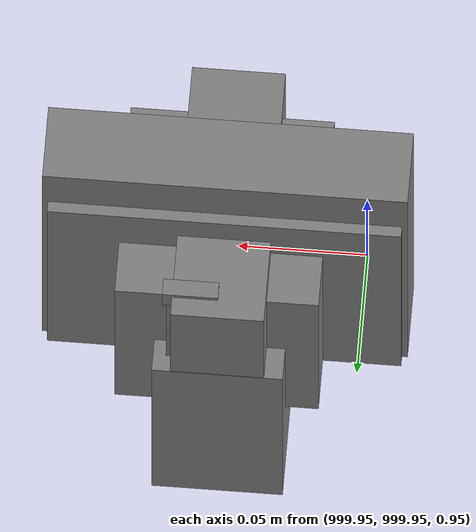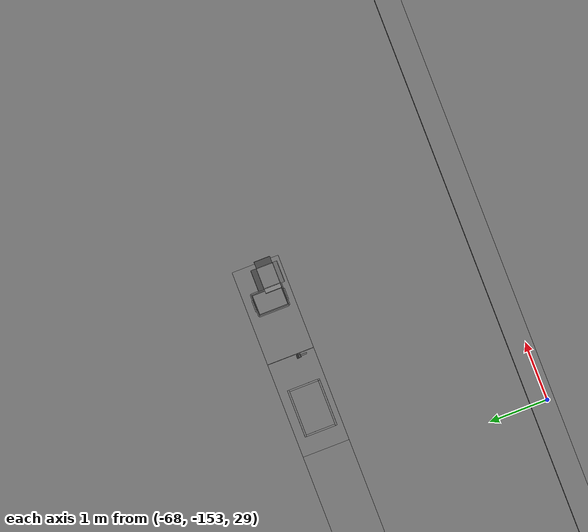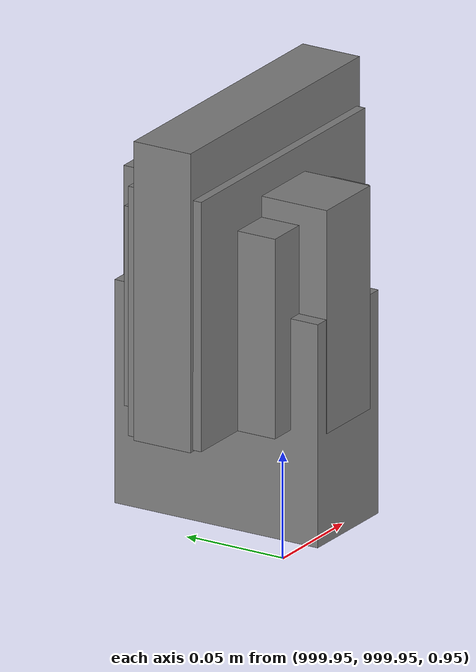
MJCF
<mujoco>
    <option gravity="0.000000000 0.000000000 -9.810000420" timestep="0.0049999999" integrator="implicitfast" density="1.225" viscosity="1.8000001e-05" noslip_iterations="10" iterations="100" sdf_iterations="50">
        <flag multiccd="disable"/>
    </option>
    <size memory="1000M"/>
    <compiler coordinate="local"/>
    <worldbody>
        <light cutoff="30" pos="0 1 1" dir="0 -1 -2"/>
        <light cutoff="30" pos="0 -1 1" dir="0 1 -2"/>
        <body pos="1000.000000000 1000.000000000 1.000000000" euler="0.000011953 0.000005123 -179.999984741" name="openloong_gripper_2f85_fix_base_usda_intel_box">
            <geom contype="1" conaffinity="1" density="1000" type="box" material="" rgba="0.500000000 0.500000000 0.500000000 1.000000000" solimp="0.899999976 0.949999988 0.001000000" friction="1.000000000 0.005000000 0.000100000" solref="0.020000000 1.000000000" margin="0" condim="3" group="0" pos="0.000000000 -0.000067139 0.000082284" quat="0.707106709 0.000000225 0.000000253 0.707106650" size="0.052800003 0.025300000 0.052800003" name="openloong_gripper_2f85_fix_base_usda_geom_D87810AA_F929_4CC5_8B2D_FCF6F8627E81"/>
            <freejoint name="openloong_gripper_2f85_fix_base_usda_intel_box_joint"/>
            <site size="0.005000000 0.005000000 0.005000000" rgba="0.500000000 0.500000000 0.500000000 1.000000000" pos="0.000000000 0.000000000 0.000000000" quat="0.999961913 0.008726500 0.000000000 0.000000000" group="0" type="sphere" name="openloong_gripper_2f85_fix_base_usda_intel_boxsite"/>
        </body>
        <body pos="-66.122650146 -149.621765137 31.167364120" euler="-35.855602264 82.377677917 171.023315430" mocap="true" name="spotlight4_SpotLight"/>
        <body pos="1000.000000000 1000.000000000 1.000000000" euler="0.000000000 0.000000000 180.000000000" name="openloong_gripper_2f85_fix_base_usda_battery_01">
            <geom contype="1" conaffinity="1" density="1000" type="box" material="" rgba="0.500000000 0.500000000 0.500000000 1.000000000" solimp="0.899999976 0.949999988 0.001000000" friction="1.000000000 0.005000000 0.000100000" solref="0.020000000 1.000000000" margin="0" condim="3" group="0" pos="-0.011123657 -0.041940309 0.101691343" quat="1.000000000 0.000000000 0.000000000 0.000000000" size="0.010800000 0.003375000 0.004725000" name="openloong_gripper_2f85_fix_base_usda_geom_30B6EC1A_55DA_451E_A4CC_91EEA023E440"/>
            <geom contype="1" conaffinity="1" density="1000" type="box" material="" rgba="0.500000000 0.500000000 0.500000000 1.000000000" solimp="0.899999976 0.949999988 0.001000000" friction="1.000000000 0.005000000 0.000100000" solref="0.020000000 1.000000000" margin="0" condim="3" group="0" pos="-0.010876465 -0.044247437 0.047066893" quat="0.998702705 -0.050920475 0.000000000 0.000000000" size="0.009450001 0.002700000 0.024975000" name="openloong_gripper_2f85_fix_base_usda_geom_AF8BD7DE_F5CB_4287_BB67_A8B566B3A21C"/>
            <geom contype="1" conaffinity="1" density="1000" type="box" material="" rgba="0.500000000 0.500000000 0.500000000 1.000000000" solimp="0.899999976 0.949999988 0.001000000" friction="1.000000000 0.005000000 0.000100000" solref="0.020000000 1.000000000" margin="0" condim="3" group="0" pos="-0.001235962 -0.000659180 0.047381196" quat="1.000000000 0.000000000 0.000000000 0.000000000" size="0.039420001 0.039150000 0.047250003" name="openloong_gripper_2f85_fix_base_usda_geom_EE287325_BEDC_45CA_B866_BCA113577A21"/>
            <geom contype="1" conaffinity="1" density="1000" type="box" material="" rgba="0.500000000 0.500000000 0.500000000 1.000000000" solimp="0.899999976 0.949999988 0.001000000" friction="1.000000000 0.005000000 0.000100000" solref="0.020000000 1.000000000" margin="0" condim="3" group="0" pos="-0.010876465 -0.039138794 0.009851727" quat="1.000000000 0.000000000 0.000000000 0.000000000" size="0.009450001 0.010800000 0.013500000" name="openloong_gripper_2f85_fix_base_usda_geom_520D0D4F_E385_4C36_9779_FA899036E01C"/>
            <geom contype="1" conaffinity="1" density="1000" type="box" material="" rgba="0.500000000 0.500000000 0.500000000 1.000000000" solimp="0.899999976 0.949999988 0.001000000" friction="1.000000000 0.005000000 0.000100000" solref="0.020000000 1.000000000" margin="0" condim="3" group="0" pos="-0.010876465 -0.041528322 0.071508206" quat="1.000000000 0.000000000 0.000000000 0.000000000" size="0.009450001 0.002700000 0.027000001" name="openloong_gripper_2f85_fix_base_usda_geom_133EB3C8_307F_4F94_A9D6_4D2AB08D69B5"/>
            <freejoint name="openloong_gripper_2f85_fix_base_usda_battery_01_joint"/>
            <site size="0.005000000 0.005000000 0.005000000" rgba="0.500000000 0.500000000 0.500000000 1.000000000" pos="0.000000000 0.000000000 0.000000000" quat="0.999961913 0.008726500 0.000000000 0.000000000" group="0" type="sphere" name="openloong_gripper_2f85_fix_base_usda_battery_01site"/>
        </body>
        <body pos="-66.348770142 -149.642440796 31.164052963" euler="27.949464798 -5.847482204 122.298980713" mocap="true" name="spotlight3_SpotLight"/>
        <body pos="1000.000000000 1000.000000000 1.000000000" euler="0.000000000 0.000000000 180.000000000" name="openloong_gripper_2f85_fix_base_usda_cpu_fan">
            <geom contype="1" conaffinity="1" density="1000" type="box" material="" rgba="0.500000000 0.500000000 0.500000000 1.000000000" solimp="0.899999976 0.949999988 0.001000000" friction="1.000000000 0.005000000 0.000100000" solref="0.020000000 1.000000000" margin="0" condim="3" group="0" pos="0.000000000 0.000000000 0.070034981" quat="0.000000000 0.000000000 0.000000000 1.000000000" size="0.070700005 0.014699999 0.070700005" name="openloong_gripper_2f85_fix_base_usda_geom_2F48E88D_FE4D_4C0E_BE0A_B1FA88245474"/>
            <freejoint name="openloong_gripper_2f85_fix_base_usda_cpu_fan_joint"/>
            <site size="0.005000000 0.005000000 0.005000000" rgba="0.500000000 0.500000000 0.500000000 1.000000000" pos="0.000000000 0.000000000 0.000000000" quat="0.999961913 0.008726535 0.000000000 0.000000000" group="0" type="sphere" name="openloong_gripper_2f85_fix_base_usda_cpu_fancsite"/>
        </body>
        <body pos="1000.000000000 1000.000000000 1.000000000" euler="0.000000000 0.000000000 180.000000000" name="openloong_gripper_2f85_fix_base_usda_wifi_box">
            <geom contype="1" conaffinity="1" density="1000" type="box" material="" rgba="0.500000000 0.500000000 0.500000000 1.000000000" solimp="0.899999976 0.949999988 0.001000000" friction="1.000000000 0.005000000 0.000100000" solref="0.020000000 1.000000000" margin="0" condim="3" group="0" pos="0.000000000 0.000000000 0.058978677" quat="0.000000000 0.000000047 0.000000000 1.000000000" size="0.068499997 0.018999999 0.059000000" name="openloong_gripper_2f85_fix_base_usda_geom_5B7148FF_7E2D_4365_8EED_7174CB278037"/>
            <freejoint name="openloong_gripper_2f85_fix_base_usda_wifi_box_joint"/>
            <site size="0.005000000 0.005000000 0.005000000" rgba="0.500000000 0.500000000 0.500000000 1.000000000" pos="0.000000000 0.000000000 0.000000000" quat="0.999961913 0.008726500 0.000000000 0.000000000" group="0" type="sphere" name="openloong_gripper_2f85_fix_base_usda_wifi_boxsite"/>
        </body>
        <body pos="-66.289093018 -149.706359863 31.164842606" euler="7.755295277 15.252447128 36.749794006" mocap="true" name="spotlight6_SpotLight"/>
        <body pos="1000.000000000 999.999938965 1.000000000" euler="0.000000000 0.000000000 180.000000000" name="openloong_gripper_2f85_fix_base_usda_intelcore_i5">
            <geom contype="1" conaffinity="1" density="1000" type="box" material="" rgba="0.500000000 0.500000000 0.500000000 1.000000000" solimp="0.899999976 0.949999988 0.001000000" friction="1.000000000 0.005000000 0.000100000" solref="0.020000000 1.000000000" margin="0" condim="3" group="0" pos="0.000000000 0.000000000 0.051722717" quat="0.707106709 0.000000000 0.000000000 -0.707106769" size="0.052800000 0.018080002 0.052800000" name="openloong_gripper_2f85_fix_base_usda_geom_33D93923_F763_4A93_8B44_87799DDC5C06"/>
            <freejoint name="openloong_gripper_2f85_fix_base_usda_intelcore_i5_joint"/>
            <site size="0.005000000 0.005000000 0.005000000" rgba="0.500000000 0.500000000 0.500000000 1.000000000" pos="0.000000000 0.000000000 0.000000000" quat="0.999961913 0.008726534 0.000000000 0.000000000" group="0" type="sphere" name="openloong_gripper_2f85_fix_base_usda_intelcore_i5site"/>
        </body>
        <body pos="-64.866622925 -149.383972168 30.183746338" euler="89.999984741 89.999946594 0.000000000" name="openloong_gripper_2f85_fix_base_usda_bluebox_01">
            <geom contype="1" conaffinity="1" density="1000" type="box" material="" rgba="0.500000000 0.500000000 0.500000000 1.000000000" solimp="0.899999976 0.949999988 0.001000000" friction="1.000000000 0.005000000 0.000100000" solref="0.020000000 1.000000000" margin="0" condim="3" group="0" pos="0.276580811 0.187225342 0.000068665" quat="0.707106948 0.000077471 0.707106352 0.000077486" size="0.100000001 0.057999998 0.010000000" name="openloong_gripper_2f85_fix_base_usda_geom_B3C34FA0_11FF_46DE_8022_34BFC7E861ED"/>
            <geom contype="1" conaffinity="1" density="1000" type="box" material="" rgba="0.500000000 0.500000000 0.500000000 1.000000000" solimp="0.899999976 0.949999988 0.001000000" friction="1.000000000 0.005000000 0.000100000" solref="0.020000000 1.000000000" margin="0" condim="3" group="0" pos="0.000000000 0.002883911 0.000000000" quat="0.999999881 0.000000000 0.000000000 0.000000000" size="0.254000008 0.003000000 0.172000006" name="openloong_gripper_2f85_fix_base_usda_geom_D6AA36F0_9E47_463F_903F_57142860B6CE"/>
            <geom contype="1" conaffinity="1" density="1000" type="box" material="" rgba="0.500000000 0.500000000 0.500000000 1.000000000" solimp="0.899999976 0.949999988 0.001000000" friction="1.000000000 0.005000000 0.000100000" solref="0.020000000 1.000000000" margin="0" condim="3" group="0" pos="0.000000000 0.124874115 0.173484802" quat="0.999796331 0.020176515 -0.000000015 0.000000030" size="0.259999990 0.119999997 0.007000000" name="openloong_gripper_2f85_fix_base_usda_geom_1A6A536A_F6AB_4357_AF43_13028BC15D7E"/>
            <geom contype="1" conaffinity="1" density="1000" type="box" material="" rgba="0.500000000 0.500000000 0.500000000 1.000000000" solimp="0.899999976 0.949999988 0.001000000" friction="1.000000000 0.005000000 0.000100000" solref="0.020000000 1.000000000" margin="0" condim="3" group="0" pos="0.000000000 0.124874115 -0.173469543" quat="0.999796331 -0.020176545 -0.000000015 0.000000000" size="0.259999990 0.119999997 0.007000000" name="openloong_gripper_2f85_fix_base_usda_geom_244D87CA_D226_485D_8150_091A1087DF8C"/>
            <geom contype="1" conaffinity="1" density="1000" type="box" material="" rgba="0.500000000 0.500000000 0.500000000 1.000000000" solimp="0.899999976 0.949999988 0.001000000" friction="1.000000000 0.005000000 0.000100000" solref="0.020000000 1.000000000" margin="0" condim="3" group="0" pos="0.000000000 0.214008331 0.188980103" quat="0.999912977 0.013176724 0.000000015 0.000000000" size="0.259999990 0.029999999 0.012500000" name="openloong_gripper_2f85_fix_base_usda_geom_88FDA45B_6E87_4E97_B472_24EFCE98EE07"/>
            <geom contype="1" conaffinity="1" density="1000" type="box" material="" rgba="0.500000000 0.500000000 0.500000000 1.000000000" solimp="0.899999976 0.949999988 0.001000000" friction="1.000000000 0.005000000 0.000100000" solref="0.020000000 1.000000000" margin="0" condim="3" group="0" pos="-0.258361816 0.125289917 0.001876831" quat="0.702796936 -0.020792112 0.710783124 0.020769298" size="0.189999998 0.119999997 0.009000000" name="openloong_gripper_2f85_fix_base_usda_geom_7164AAB8_3B03_43E3_9835_DB2614247668"/>
            <geom contype="1" conaffinity="1" density="1000" type="box" material="" rgba="0.500000000 0.500000000 0.500000000 1.000000000" solimp="0.899999976 0.949999988 0.001000000" friction="1.000000000 0.005000000 0.000100000" solref="0.020000000 1.000000000" margin="0" condim="3" group="0" pos="0.000000000 0.214008331 -0.188980103" quat="0.999912977 -0.013176769 0.000000030 0.000000015" size="0.259999990 0.029999999 0.012500000" name="openloong_gripper_2f85_fix_base_usda_geom_25862047_5C95_4694_AB35_42E3159549E5"/>
            <geom contype="1" conaffinity="1" density="1000" type="box" material="" rgba="0.500000000 0.500000000 0.500000000 1.000000000" solimp="0.899999976 0.949999988 0.001000000" friction="1.000000000 0.005000000 0.000100000" solref="0.020000000 1.000000000" margin="0" condim="3" group="0" pos="-0.276611328 0.187225342 0.000068665" quat="0.707106650 0.000077441 0.707106709 0.000077456" size="0.100000001 0.057999998 0.010000000" name="openloong_gripper_2f85_fix_base_usda_geom_7AF79401_479D_4D66_96D1_74F5E13A338C"/>
            <geom contype="1" conaffinity="1" density="1000" type="box" material="" rgba="0.500000000 0.500000000 0.500000000 1.000000000" solimp="0.899999976 0.949999988 0.001000000" friction="1.000000000 0.005000000 0.000100000" solref="0.020000000 1.000000000" margin="0" condim="3" group="0" pos="0.258331299 0.125289917 0.001876831" quat="0.702851415 0.018856421 0.710823774 -0.019329369" size="0.189999998 0.119999997 0.009000000" name="openloong_gripper_2f85_fix_base_usda_geom_619EE731_9487_45D0_AD08_78543DBBB44C"/>
            <freejoint name="openloong_gripper_2f85_fix_base_usda_bluebox_01_joint"/>
            <site size="0.005000000 0.005000000 0.005000000" rgba="0.500000000 0.500000000 0.500000000 1.000000000" pos="0.000000000 0.000000000 0.000000000" quat="0.999961913 0.008726534 0.000000000 0.000000000" group="0" type="sphere" name="openloong_gripper_2f85_fix_base_usda_bluebox_01site"/>
        </body>
        <body pos="-64.496299744 -149.491867065 30.235729218" euler="0.000000000 0.000000000 89.999946594" name="openloong_gripper_2f85_fix_base_usda_cardboardbox_01">
            <geom contype="1" conaffinity="1" density="1000" type="box" material="" rgba="0.500000000 0.500000000 0.500000000 1.000000000" solimp="0.899999976 0.949999988 0.001000000" friction="1.000000000 0.005000000 0.000100000" solref="0.020000000 1.000000000" margin="0" condim="3" group="0" pos="-0.003166199 -0.004086494 0.005052090" quat="1.000000000 0.000000000 0.000000000 0.000000000" size="0.142499998 0.177500010 0.005000000" name="openloong_gripper_2f85_fix_base_usda_geom_6C1D4B8B_D0E7_47F6_958B_D79AAFDAF178"/>
            <geom contype="1" conaffinity="1" density="1000" type="box" material="" rgba="0.500000000 0.500000000 0.500000000 1.000000000" solimp="0.899999976 0.949999988 0.001000000" friction="1.000000000 0.005000000 0.000100000" solref="0.020000000 1.000000000" margin="0" condim="3" group="0" pos="-0.003166199 0.170316696 0.150570869" quat="1.000000000 0.000000000 0.000000000 0.000000000" size="0.142499998 0.005000000 0.149999991" name="openloong_gripper_2f85_fix_base_usda_geom_1FF09695_F735_4151_BA2A_A76A91F781D9"/>
            <geom contype="1" conaffinity="1" density="1000" type="box" material="" rgba="0.500000000 0.500000000 0.500000000 1.000000000" solimp="0.899999976 0.949999988 0.001000000" friction="1.000000000 0.005000000 0.000100000" solref="0.020000000 1.000000000" margin="0" condim="3" group="0" pos="-0.147399902 -0.005307198 0.150570869" quat="1.000000000 0.000000000 0.000000000 0.000000000" size="0.005000000 0.177500010 0.149999991" name="openloong_gripper_2f85_fix_base_usda_geom_C435B6B4_D3C4_4B37_B064_72D666B6D4B9"/>
            <geom contype="1" conaffinity="1" density="1000" type="box" material="" rgba="0.500000000 0.500000000 0.500000000 1.000000000" solimp="0.899999976 0.949999988 0.001000000" friction="1.000000000 0.005000000 0.000100000" solref="0.020000000 1.000000000" margin="0" condim="3" group="0" pos="0.140275955 -0.005307198 0.150570869" quat="1.000000000 0.000000000 0.000000000 0.000000000" size="0.005000000 0.177500010 0.149999991" name="openloong_gripper_2f85_fix_base_usda_geom_BEFE93BC_EA9E_452B_9D79_44FCD1F90CFB"/>
            <geom contype="1" conaffinity="1" density="1000" type="box" material="" rgba="0.500000000 0.500000000 0.500000000 1.000000000" solimp="0.899999976 0.949999988 0.001000000" friction="1.000000000 0.005000000 0.000100000" solref="0.020000000 1.000000000" margin="0" condim="3" group="0" pos="-0.003166199 -0.181550980 0.150570869" quat="1.000000000 0.000000000 0.000000000 0.000000000" size="0.142499998 0.005000000 0.149999991" name="openloong_gripper_2f85_fix_base_usda_geom_01DA2209_F5B5_498F_A735_CBBE9844AC23"/>
            <freejoint name="openloong_gripper_2f85_fix_base_usda_cardboardbox_01_joint"/>
            <site size="0.005000000 0.005000000 0.005000000" rgba="0.500000000 0.500000000 0.500000000 1.000000000" pos="0.000000000 0.000000000 0.000000000" quat="0.999961913 0.008726535 0.000000000 0.000000000" group="0" type="sphere" name="openloong_gripper_2f85_fix_base_usda_site_02EF06A0_A6A9_460D_80CA_9955F0F2ACFF"/>
            <body pos="0.139160156 -0.004048347 0.301930904" euler="-179.999954224 49.383502960 179.999954224" name="openloong_gripper_2f85_fix_base_usda_A1_006">
                <geom contype="1" conaffinity="1" density="1000" type="box" material="" rgba="0.500000000 0.500000000 0.500000000 1.000000000" solimp="0.899999976 0.949999988 0.001000000" friction="1.000000000 0.005000000 0.000100000" solref="0.020000000 1.000000000" margin="0" condim="3" group="0" pos="-0.071587563 0.000009537 0.001745224" quat="0.999999881 0.000000000 0.000000000 0.000000000" size="0.071249999 0.179999992 0.002500000" name="openloong_gripper_2f85_fix_base_usda_geom_909332AB_8F46_4472_89B8_8DAB1E690867"/>
                <joint armature="0" stiffness="0.07" damping="0.0099999998" axis="0.000000 1.000000 0.000000" type="hinge" name="openloong_gripper_2f85_fix_base_usda_A1_006"/>
            </body>
            <body pos="-0.145902634 -0.004086494 0.301938057" euler="-180.000000000 -60.000011444 -180.000000000" name="openloong_gripper_2f85_fix_base_usda_A2_006">
                <geom contype="1" conaffinity="1" density="1000" type="box" material="" rgba="0.500000000 0.500000000 0.500000000 1.000000000" solimp="0.899999976 0.949999988 0.001000000" friction="1.000000000 0.005000000 0.000100000" solref="0.020000000 1.000000000" margin="0" condim="3" group="0" pos="0.071268082 0.000009537 0.002717972" quat="0.000002921 0.000000000 -0.000000030 0.999999881" size="0.071249999 0.179999992 0.002500000" name="openloong_gripper_2f85_fix_base_usda_geom_27ECFECE_8549_4711_A5B0_03846847AEF1"/>
                <joint armature="0" stiffness="0.07" damping="0.0099999998" axis="0.000000 1.000000 0.000000" type="hinge" name="openloong_gripper_2f85_fix_base_usda_A2_006"/>
            </body>
            <body pos="-0.003385544 0.175991058 0.301930904" euler="-125.858116150 -0.000004561 0.000002331" name="openloong_gripper_2f85_fix_base_usda_B2_006">
                <geom contype="1" conaffinity="1" density="1000" type="box" material="" rgba="0.500000000 0.500000000 0.500000000 1.000000000" solimp="0.899999976 0.949999988 0.001000000" friction="1.000000000 0.005000000 0.000100000" solref="0.020000000 1.000000000" margin="0" condim="3" group="0" pos="0.000009537 -0.070939064 -0.002470016" quat="0.999614120 0.027776197 -0.000000015 0.000000030" size="0.137500003 0.064999998 0.005000000" name="openloong_gripper_2f85_fix_base_usda_geom_881AE311_E6C7_4909_8EAE_08A8C86C9EF6"/>
                <joint armature="0" stiffness="0.07" damping="0.0099999998" axis="1.000000 0.000000 0.000000" type="hinge" name="openloong_gripper_2f85_fix_base_usda_B2_006"/>
            </body>
            <body pos="-0.003385544 -0.184140205 0.301938057" euler="147.805557251 0.000000000 0.000000000" name="openloong_gripper_2f85_fix_base_usda_B1_006">
                <geom contype="1" conaffinity="1" density="1000" type="box" material="" rgba="0.500000000 0.500000000 0.500000000 1.000000000" solimp="0.899999976 0.949999988 0.001000000" friction="1.000000000 0.005000000 0.000100000" solref="0.020000000 1.000000000" margin="0" condim="3" group="0" pos="-0.000028610 0.070202351 -0.002703667" quat="0.999614179 -0.027776167 0.000000000 0.000000000" size="0.137500003 0.064999998 0.005000000" name="openloong_gripper_2f85_fix_base_usda_geom_F8824B87_E980_494D_9D96_7DA9403BF7A9"/>
                <joint armature="0" stiffness="0.07" damping="0.0099999998" axis="1.000000 0.000000 0.000000" type="hinge" name="openloong_gripper_2f85_fix_base_usda_B1_006"/>
            </body>
        </body>
        <body pos="-65.882858276 -149.481979370 30.229999542" euler="-64.487716675 0.000000000 0.000000000" name="openloong_gripper_2f85_fix_base_usda_Barcode">
            <geom contype="1" conaffinity="1" density="1000" type="box" material="" rgba="0.500000000 0.500000000 0.500000000 1.000000000" solimp="0.899999976 0.949999988 0.001000000" friction="1.000000000 0.005000000 0.000100000" solref="0.020000000 1.000000000" margin="0" condim="3" group="0" pos="0.000000000 0.013038635 0.001419067" quat="0.000000000 0.000000000 0.000000000 1.000000119" size="0.034000002 0.010000000 0.017999999" name="openloong_gripper_2f85_fix_base_usda_geom_2F6D4245_7CC1_493E_9362_5E2FABA69A37"/>
            <geom contype="1" conaffinity="1" density="1000" type="box" material="" rgba="0.500000000 0.500000000 0.500000000 1.000000000" solimp="0.899999976 0.949999988 0.001000000" friction="1.000000000 0.005000000 0.000100000" solref="0.020000000 1.000000000" margin="0" condim="3" group="0" pos="0.000000000 -0.035301208 -0.007095337" quat="0.000000000 0.000000000 -0.043619365 0.999048233" size="0.028999999 0.010000000 0.020000000" name="openloong_gripper_2f85_fix_base_usda_geom_45BEC662_BCD7_45EE_9D63_81D104F18876"/>
            <geom contype="1" conaffinity="1" density="1000" type="box" material="" rgba="0.500000000 0.500000000 0.500000000 1.000000000" solimp="0.899999976 0.949999988 0.001000000" friction="1.000000000 0.005000000 0.000100000" solref="0.020000000 1.000000000" margin="0" condim="3" group="0" pos="0.000000000 -0.043411255 -0.011749268" quat="0.922262907 0.386563420 0.000000000 0.000000000" size="0.026000001 0.010000000 0.020000000" name="openloong_gripper_2f85_fix_base_usda_geom_59A049AC_6730_4214_8211_684B774A02EC"/>
            <geom contype="1" conaffinity="1" density="1000" type="box" material="" rgba="0.500000000 0.500000000 0.500000000 1.000000000" solimp="0.899999976 0.949999988 0.001000000" friction="1.000000000 0.005000000 0.000100000" solref="0.020000000 1.000000000" margin="0" condim="3" group="0" pos="0.000000000 -0.016967773 -0.031860352" quat="0.000000000 0.000000000 0.000000000 1.000000119" size="0.008000000 0.010000000 0.013000000" name="openloong_gripper_2f85_fix_base_usda_geom_19743082_F717_4E60_9D1C_C9C53AB1E7DF"/>
            <geom contype="1" conaffinity="1" density="1000" type="box" material="" rgba="0.500000000 0.500000000 0.500000000 1.000000000" solimp="0.899999976 0.949999988 0.001000000" friction="1.000000000 0.005000000 0.000100000" solref="0.020000000 1.000000000" margin="0" condim="3" group="0" pos="0.000000000 -0.001869202 0.000312805" quat="0.953716993 0.300705761 0.000000000 0.000000000" size="0.032000002 0.010000000 0.018999999" name="openloong_gripper_2f85_fix_base_usda_geom_A11CFD1E_5EF8_4DB5_9AEB_47DAD450CFAD"/>
            <geom contype="1" conaffinity="1" density="1000" type="box" material="" rgba="0.500000000 0.500000000 0.500000000 1.000000000" solimp="0.899999976 0.949999988 0.001000000" friction="1.000000000 0.005000000 0.000100000" solref="0.020000000 1.000000000" margin="0" condim="3" group="0" pos="0.000000000 -0.019531250 -0.003173828" quat="0.953716993 0.300705761 0.000000000 0.000000000" size="0.030999999 0.010000000 0.020000000" name="openloong_gripper_2f85_fix_base_usda_geom_21384FF3_78E0_4C18_A540_88710F2B0AEB"/>
            <geom contype="1" conaffinity="1" density="1000" type="box" material="" rgba="0.500000000 0.500000000 0.500000000 1.000000000" solimp="0.899999976 0.949999988 0.001000000" friction="1.000000000 0.005000000 0.000100000" solref="0.020000000 1.000000000" margin="0" condim="3" group="0" pos="0.000000000 -0.035301208 -0.007095337" quat="0.953716993 0.300705761 0.000000000 0.000000000" size="0.028999999 0.010000000 0.020000000" name="openloong_gripper_2f85_fix_base_usda_geom_6B38C9A3_DC55_4748_BE2F_3ABFDB554D95"/>
            <geom contype="1" conaffinity="1" density="1000" type="box" material="" rgba="0.500000000 0.500000000 0.500000000 1.000000000" solimp="0.899999976 0.949999988 0.001000000" friction="1.000000000 0.005000000 0.000100000" solref="0.020000000 1.000000000" margin="0" condim="3" group="0" pos="0.000000000 -0.042617798 -0.071121216" quat="0.000000000 0.000000000 0.000000000 1.000000119" size="0.013000000 0.021000000 0.059999999" name="openloong_gripper_2f85_fix_base_usda_geom_A4357F91_C2C4_4AAA_80CE_05D429E72C14"/>
            <freejoint name="openloong_gripper_2f85_fix_base_usda_Barcode_joint"/>
            <site size="0.005000000 0.005000000 0.005000000" rgba="0.500000000 0.500000000 0.500000000 1.000000000" pos="0.000000000 0.000000000 0.000000000" quat="1.000000000 0.000000000 0.000000000 0.000000000" group="0" type="sphere" name="openloong_gripper_2f85_fix_base_usda_Barcode_site"/>
        </body>
        <body pos="-66.745018005 -149.392349243 30.184000015" euler="0.000000000 0.000000000 89.999946594" name="[22330228238387]_Basket_01">
            <geom contype="1" conaffinity="1" density="1000" type="box" material="" rgba="0.500000000 0.500000000 0.500000000 1.000000000" solimp="0.899999976 0.949999988 0.001000000" friction="1.000000000 0.005000000 0.000100000" solref="0.020000000 1.000000000" margin="0" condim="3" group="0" pos="-0.052425385 0.389207840 0.089787483" quat="0.707107008 0.000000000 0.000000000 0.707106411" size="0.014249999 0.014249999 0.059999999" name="[22330228238387]_geom_CA3F804A_963A_4670_A07C_41EA25B90119"/>
            <geom contype="1" conaffinity="1" density="1000" type="box" material="" rgba="0.500000000 0.500000000 0.500000000 1.000000000" solimp="0.899999976 0.949999988 0.001000000" friction="1.000000000 0.005000000 0.000100000" solref="0.020000000 1.000000000" margin="0" condim="3" group="0" pos="0.264015198 -0.133043289 0.089787483" quat="0.707107008 0.000000000 0.000000000 0.707106411" size="0.014249999 0.014249999 0.059999999" name="[22330228238387]_geom_AD2B3F26_8CEF_4D9B_9005_7F5A9CC46705"/>
            <geom contype="1" conaffinity="1" density="1000" type="box" material="" rgba="0.500000000 0.500000000 0.500000000 1.000000000" solimp="0.899999976 0.949999988 0.001000000" friction="1.000000000 0.005000000 0.000100000" solref="0.020000000 1.000000000" margin="0" condim="3" group="0" pos="-0.264015198 -0.265548706 0.089793205" quat="0.707107008 0.000000000 0.000000000 0.707106411" size="0.014249999 0.014249999 0.059999999" name="[22330228238387]_geom_35813B16_2E6B_45FF_840D_9F026185447A"/>
            <geom contype="1" conaffinity="1" density="1000" type="box" material="" rgba="0.500000000 0.500000000 0.500000000 1.000000000" solimp="0.899999976 0.949999988 0.001000000" friction="1.000000000 0.005000000 0.000100000" solref="0.020000000 1.000000000" margin="0" condim="3" group="0" pos="-0.160263062 -0.389322281 0.089793205" quat="0.707107008 0.000000000 0.000000000 0.707106411" size="0.014249999 0.014249999 0.059999999" name="[22330228238387]_geom_F3E049DB_173C_4279_86BA_2C3489E7D974"/>
            <geom contype="1" conaffinity="1" density="1000" type="box" material="" rgba="0.500000000 0.500000000 0.500000000 1.000000000" solimp="0.899999976 0.949999988 0.001000000" friction="1.000000000 0.005000000 0.000100000" solref="0.020000000 1.000000000" margin="0" condim="3" group="0" pos="0.162265778 -0.389322281 0.089787483" quat="0.707107008 0.000000000 0.000000000 0.707106411" size="0.014249999 0.014249999 0.059999999" name="[22330228238387]_geom_507A08F5_F309_40DD_BA07_D18F92C74C24"/>
            <geom contype="1" conaffinity="1" density="1000" type="box" material="" rgba="0.500000000 0.500000000 0.500000000 1.000000000" solimp="0.899999976 0.949999988 0.001000000" friction="1.000000000 0.005000000 0.000100000" solref="0.020000000 1.000000000" margin="0" condim="3" group="0" pos="0.264015198 0.389207840 0.089787483" quat="0.707107008 0.000000000 0.000000000 0.707106411" size="0.014249999 0.014249999 0.059999999" name="[22330228238387]_geom_FD9962ED_1ED5_4B79_9CF2_6745933663FA"/>
            <geom contype="1" conaffinity="1" density="1000" type="box" material="" rgba="0.500000000 0.500000000 0.500000000 1.000000000" solimp="0.899999976 0.949999988 0.001000000" friction="1.000000000 0.005000000 0.000100000" solref="0.020000000 1.000000000" margin="0" condim="3" group="0" pos="-0.264015198 -0.133043289 0.089793205" quat="0.707107008 0.000000000 0.000000000 0.707106411" size="0.014249999 0.014249999 0.059999999" name="[22330228238387]_geom_057A45D2_6622_4B4A_A59B_92226F77DFF8"/>
            <geom contype="1" conaffinity="1" density="1000" type="box" material="" rgba="0.500000000 0.500000000 0.500000000 1.000000000" solimp="0.899999976 0.949999988 0.001000000" friction="1.000000000 0.005000000 0.000100000" solref="0.020000000 1.000000000" margin="0" condim="3" group="0" pos="-0.264026642 0.269256592 0.089793205" quat="0.707107008 0.000000000 0.000000000 0.707106411" size="0.014249999 0.014249999 0.059999999" name="[22330228238387]_geom_34A9C42A_2D9E_4FD7_BDBB_E1CC5C1684D2"/>
            <geom contype="1" conaffinity="1" density="1000" type="box" material="" rgba="0.500000000 0.500000000 0.500000000 1.000000000" solimp="0.899999976 0.949999988 0.001000000" friction="1.000000000 0.005000000 0.000100000" solref="0.020000000 1.000000000" margin="0" condim="3" group="0" pos="0.054462433 0.389207840 0.089787483" quat="0.707107008 0.000000000 0.000000000 0.707106411" size="0.014249999 0.014249999 0.059999999" name="[22330228238387]_geom_B1135F44_8335_4460_B437_51CE02B5F9C1"/>
            <geom contype="1" conaffinity="1" density="1000" type="box" material="" rgba="0.500000000 0.500000000 0.500000000 1.000000000" solimp="0.899999976 0.949999988 0.001000000" friction="1.000000000 0.005000000 0.000100000" solref="0.020000000 1.000000000" margin="0" condim="3" group="0" pos="0.054462433 -0.389322281 0.089787483" quat="0.707107008 0.000000000 0.000000000 0.707106411" size="0.014249999 0.014249999 0.059999999" name="[22330228238387]_geom_3E7C69AA_3DFF_48D1_AC7D_247D4BE31213"/>
            <geom contype="1" conaffinity="1" density="1000" type="box" material="" rgba="0.500000000 0.500000000 0.500000000 1.000000000" solimp="0.899999976 0.949999988 0.001000000" friction="1.000000000 0.005000000 0.000100000" solref="0.020000000 1.000000000" margin="0" condim="3" group="0" pos="0.264015198 0.269256592 0.089793205" quat="0.707107008 0.000000000 0.000000000 0.707106411" size="0.014249999 0.014249999 0.059999999" name="[22330228238387]_geom_9C103959_48BD_4B55_8140_B86886B9FB2F"/>
            <geom contype="1" conaffinity="1" density="1000" type="box" material="" rgba="0.500000000 0.500000000 0.500000000 1.000000000" solimp="0.899999976 0.949999988 0.001000000" friction="1.000000000 0.005000000 0.000100000" solref="0.020000000 1.000000000" margin="0" condim="3" group="0" pos="0.264015198 -0.389322281 0.089787483" quat="0.707107008 0.000000000 0.000000000 0.707106411" size="0.014249999 0.014249999 0.059999999" name="[22330228238387]_geom_9F40FE9D_D2CE_4BB3_89B2_78221BC9EAE9"/>
            <geom contype="1" conaffinity="1" density="1000" type="box" material="" rgba="0.500000000 0.500000000 0.500000000 1.000000000" solimp="0.899999976 0.949999988 0.001000000" friction="1.000000000 0.005000000 0.000100000" solref="0.020000000 1.000000000" margin="0" condim="3" group="0" pos="0.000000000 0.000000000 0.015998840" quat="0.707107008 0.000000000 0.000000000 0.707106411" size="0.403499991 0.279000014 0.015750000" name="[22330228238387]_geom_F2CED453_3E1B_4F43_BD16_8B9505EB0A81"/>
            <geom contype="1" conaffinity="1" density="1000" type="box" material="" rgba="0.500000000 0.500000000 0.500000000 1.000000000" solimp="0.899999976 0.949999988 0.001000000" friction="1.000000000 0.005000000 0.000100000" solref="0.020000000 1.000000000" margin="0" condim="3" group="0" pos="0.000000000 -0.389476776 0.163619041" quat="0.707107008 0.000000000 0.000000000 0.707106411" size="0.015000000 0.277500004 0.015750000" name="[22330228238387]_geom_5EE534EE_466A_437E_A9D3_DE98FA9222A8"/>
            <geom contype="1" conaffinity="1" density="1000" type="box" material="" rgba="0.500000000 0.500000000 0.500000000 1.000000000" solimp="0.899999976 0.949999988 0.001000000" friction="1.000000000 0.005000000 0.000100000" solref="0.020000000 1.000000000" margin="0" condim="3" group="0" pos="0.162265778 0.389207840 0.089787483" quat="0.707107008 0.000000000 0.000000000 0.707106411" size="0.014249999 0.014249999 0.059999999" name="[22330228238387]_geom_EFD7E0B4_75DA_41A8_8D3B_F5407C0E2890"/>
            <geom contype="1" conaffinity="1" density="1000" type="box" material="" rgba="0.500000000 0.500000000 0.500000000 1.000000000" solimp="0.899999976 0.949999988 0.001000000" friction="1.000000000 0.005000000 0.000100000" solref="0.020000000 1.000000000" margin="0" condim="3" group="0" pos="0.000000000 0.389471054 0.163619041" quat="0.707107008 0.000000000 0.000000000 0.707106411" size="0.015000000 0.277500004 0.015750000" name="[22330228238387]_geom_844EC436_BA81_46F5_B45A_0422252B5ACB"/>
            <geom contype="1" conaffinity="1" density="1000" type="box" material="" rgba="0.500000000 0.500000000 0.500000000 1.000000000" solimp="0.899999976 0.949999988 0.001000000" friction="1.000000000 0.005000000 0.000100000" solref="0.020000000 1.000000000" margin="0" condim="3" group="0" pos="-0.263511658 0.000000000 0.163619041" quat="0.707107008 0.000000000 0.000000000 0.707106411" size="0.403499991 0.015000000 0.015750000" name="[22330228238387]_geom_05F4FF07_6CB9_4F9B_8A7C_DBCFDF0590DF"/>
            <geom contype="1" conaffinity="1" density="1000" type="box" material="" rgba="0.500000000 0.500000000 0.500000000 1.000000000" solimp="0.899999976 0.949999988 0.001000000" friction="1.000000000 0.005000000 0.000100000" solref="0.020000000 1.000000000" margin="0" condim="3" group="0" pos="-0.264015198 0.141334534 0.089793205" quat="0.707107008 0.000000000 0.000000000 0.707106411" size="0.014249999 0.014249999 0.059999999" name="[22330228238387]_geom_3B9E32EB_3D07_4815_8ABE_E3D9CD39F112"/>
            <geom contype="1" conaffinity="1" density="1000" type="box" material="" rgba="0.500000000 0.500000000 0.500000000 1.000000000" solimp="0.899999976 0.949999988 0.001000000" friction="1.000000000 0.005000000 0.000100000" solref="0.020000000 1.000000000" margin="0" condim="3" group="0" pos="0.264015198 -0.265548706 0.089787483" quat="0.707107008 0.000000000 0.000000000 0.707106411" size="0.014249999 0.014249999 0.059999999" name="[22330228238387]_geom_20D9BC82_F117_4AD5_B800_0D30936A68F0"/>
            <geom contype="1" conaffinity="1" density="1000" type="box" material="" rgba="0.500000000 0.500000000 0.500000000 1.000000000" solimp="0.899999976 0.949999988 0.001000000" friction="1.000000000 0.005000000 0.000100000" solref="0.020000000 1.000000000" margin="0" condim="3" group="0" pos="-0.160263062 0.389207840 0.089787483" quat="0.707107008 0.000000000 0.000000000 0.707106411" size="0.014249999 0.014249999 0.059999999" name="[22330228238387]_geom_BCC1DE72_1837_437A_B53F_4DD5A33206BA"/>
            <geom contype="1" conaffinity="1" density="1000" type="box" material="" rgba="0.500000000 0.500000000 0.500000000 1.000000000" solimp="0.899999976 0.949999988 0.001000000" friction="1.000000000 0.005000000 0.000100000" solref="0.020000000 1.000000000" margin="0" condim="3" group="0" pos="-0.052425385 -0.389322281 0.089787483" quat="0.707107008 0.000000000 0.000000000 0.707106411" size="0.014249999 0.014249999 0.059999999" name="[22330228238387]_geom_972BA00E_285E_493E_B02E_6D5614A0EE42"/>
            <geom contype="1" conaffinity="1" density="1000" type="box" material="" rgba="0.500000000 0.500000000 0.500000000 1.000000000" solimp="0.899999976 0.949999988 0.001000000" friction="1.000000000 0.005000000 0.000100000" solref="0.020000000 1.000000000" margin="0" condim="3" group="0" pos="-0.264026642 -0.389322281 0.089793205" quat="0.707107008 0.000000000 0.000000000 0.707106411" size="0.014249999 0.014249999 0.059999999" name="[22330228238387]_geom_3A526494_4B70_4B5A_9B22_C5D02B5C056E"/>
            <geom contype="1" conaffinity="1" density="1000" type="box" material="" rgba="0.500000000 0.500000000 0.500000000 1.000000000" solimp="0.899999976 0.949999988 0.001000000" friction="1.000000000 0.005000000 0.000100000" solref="0.020000000 1.000000000" margin="0" condim="3" group="0" pos="0.264015198 0.141334534 0.089787483" quat="0.707107008 0.000000000 0.000000000 0.707106411" size="0.014249999 0.014249999 0.059999999" name="[22330228238387]_geom_B6D8F1CF_4513_4305_A24E_64C5260B82C1"/>
            <geom contype="1" conaffinity="1" density="1000" type="box" material="" rgba="0.500000000 0.500000000 0.500000000 1.000000000" solimp="0.899999976 0.949999988 0.001000000" friction="1.000000000 0.005000000 0.000100000" solref="0.020000000 1.000000000" margin="0" condim="3" group="0" pos="-0.264015198 0.389207840 0.089793205" quat="0.707107008 0.000000000 0.000000000 0.707106411" size="0.014249999 0.014249999 0.059999999" name="[22330228238387]_geom_4F55DE22_944E_441F_8416_ED526A4D4A2E"/>
            <geom contype="1" conaffinity="1" density="1000" type="box" material="" rgba="0.500000000 0.500000000 0.500000000 1.000000000" solimp="0.899999976 0.949999988 0.001000000" friction="1.000000000 0.005000000 0.000100000" solref="0.020000000 1.000000000" margin="0" condim="3" group="0" pos="0.264015198 0.004480362 0.089787483" quat="0.707107008 0.000000000 0.000000000 0.707106411" size="0.014249999 0.014249999 0.059999999" name="[22330228238387]_geom_CD56015F_38A6_4A00_A680_D82A9EB4822A"/>
            <geom contype="1" conaffinity="1" density="1000" type="box" material="" rgba="0.500000000 0.500000000 0.500000000 1.000000000" solimp="0.899999976 0.949999988 0.001000000" friction="1.000000000 0.005000000 0.000100000" solref="0.020000000 1.000000000" margin="0" condim="3" group="0" pos="0.263694763 -0.000011444 0.163619041" quat="0.707107008 0.000000000 0.000000000 0.707106411" size="0.403499991 0.015000000 0.015750000" name="[22330228238387]_geom_F7F442D0_6735_49A0_B146_B8F49ECECF03"/>
            <geom contype="1" conaffinity="1" density="1000" type="box" material="" rgba="0.500000000 0.500000000 0.500000000 1.000000000" solimp="0.899999976 0.949999988 0.001000000" friction="1.000000000 0.005000000 0.000100000" solref="0.020000000 1.000000000" margin="0" condim="3" group="0" pos="-0.264015198 0.004480362 0.089793205" quat="0.707107008 0.000000000 0.000000000 0.707106411" size="0.014249999 0.014249999 0.059999999" name="[22330228238387]_geom_745BD907_DC3E_4248_B2EB_57CFDBAF1FEB"/>
            <freejoint name="[22330228238387]_joint_07E5A4A6_1906_4AFF_9BE2_B1B67EED9194"/>
        </body>
        <body pos="0.000000000 0.000000000 0.000000000" euler="0.000000000 0.000000000 0.000000000" name="Static Objects_Static Objects">
            <geom contype="1" conaffinity="1" density="1000" type="box" material="" rgba="0.500000000 0.500000000 0.500000000 1.000000000" solimp="0.899999976 0.949999988 0.001000000" friction="1.000000000 0.005000000 0.000100000" solref="0.020000000 1.000000000" margin="0" condim="3" group="0" pos="-67.544113159 -149.365814209 29.727830887" quat="0.500000417 0.499999970 0.499999553 0.499999970" size="0.381000012 0.319999993 0.041000001" name="Static Objects_geom_3638610F_C518_4AA9_BF59_FBDA77C15F1D"/>
            <geom contype="1" conaffinity="1" density="1000" type="box" material="" rgba="0.500000000 0.500000000 0.500000000 1.000000000" solimp="0.899999976 0.949999988 0.001000000" friction="1.000000000 0.005000000 0.000100000" solref="0.020000000 1.000000000" margin="0" condim="3" group="0" pos="-68.239501953 -149.365814209 30.086868286" quat="0.500000417 0.499999970 0.499999553 0.499999970" size="0.370999992 0.039500002 0.745000005" name="Static Objects_geom_7073C011_86F3_4FB3_BC02_DCF0C123C085"/>
            <geom contype="1" conaffinity="1" density="1000" type="box" material="" rgba="0.500000000 0.500000000 0.500000000 1.000000000" solimp="0.899999976 0.949999988 0.001000000" friction="1.000000000 0.005000000 0.000100000" solref="0.020000000 1.000000000" margin="0" condim="3" group="0" pos="-68.239501953 -149.365814209 30.147235870" quat="0.500000417 0.499999970 0.499999553 0.499999970" size="0.400000006 0.022000000 0.800000012" name="Static Objects_geom_90262090_FD69_46AB_B9E6_F1E61689C48E"/>
            <geom contype="1" conaffinity="1" density="1000" type="box" material="" rgba="0.500000000 0.500000000 0.500000000 1.000000000" solimp="0.899999976 0.949999988 0.001000000" friction="1.000000000 0.005000000 0.000100000" solref="0.020000000 1.000000000" margin="0" condim="3" group="0" pos="-68.934890747 -149.365814209 29.727830887" quat="0.500000417 0.499999970 0.499999553 0.499999970" size="0.381000012 0.319999993 0.041000001" name="Static Objects_geom_F6C58118_9A5D_4B73_8C10_9E46212B7E40"/>
            <geom contype="1" conaffinity="1" density="1000" type="box" material="" rgba="0.500000000 0.500000000 0.500000000 1.000000000" solimp="0.899999976 0.949999988 0.001000000" friction="1.000000000 0.005000000 0.000100000" solref="0.020000000 1.000000000" margin="0" condim="3" group="0" pos="-68.239501953 -149.365814209 29.561563492" quat="0.500000417 0.499999970 0.499999553 0.499999970" size="0.020000000 0.022000000 0.660000026" name="Static Objects_geom_366F5870_820B_4FCA_A7F1_5B2C6594CFD6"/>
            <geom contype="1" conaffinity="1" density="1000" type="box" material="" rgba="0.500000000 0.500000000 0.500000000 1.000000000" solimp="0.899999976 0.949999988 0.001000000" friction="1.000000000 0.005000000 0.000100000" solref="0.020000000 1.000000000" margin="0" condim="3" group="0" pos="-65.945671082 -149.365814209 29.727830887" quat="0.500000417 0.499999970 0.499999553 0.499999970" size="0.381000012 0.319999993 0.041000001" name="Static Objects_geom_B55C2504_21DA_48DD_9B99_39B77ACEB7FD"/>
            <geom contype="1" conaffinity="1" density="1000" type="box" material="" rgba="0.500000000 0.500000000 0.500000000 1.000000000" solimp="0.899999976 0.949999988 0.001000000" friction="1.000000000 0.005000000 0.000100000" solref="0.020000000 1.000000000" margin="0" condim="3" group="0" pos="-66.641059875 -149.365814209 30.086868286" quat="0.500000417 0.499999970 0.499999553 0.499999970" size="0.370999992 0.039500002 0.745000005" name="Static Objects_geom_6B1DA18F_ACD6_4D33_9D25_480355C0F442"/>
            <geom contype="1" conaffinity="1" density="1000" type="box" material="" rgba="0.500000000 0.500000000 0.500000000 1.000000000" solimp="0.899999976 0.949999988 0.001000000" friction="1.000000000 0.005000000 0.000100000" solref="0.020000000 1.000000000" margin="0" condim="3" group="0" pos="-66.641059875 -149.365814209 30.147235870" quat="0.500000417 0.499999970 0.499999553 0.499999970" size="0.400000006 0.022000000 0.800000012" name="Static Objects_geom_E4C6D37D_5123_4109_B6D7_FCC7FFDDE1C9"/>
            <geom contype="1" conaffinity="1" density="1000" type="box" material="" rgba="0.500000000 0.500000000 0.500000000 1.000000000" solimp="0.899999976 0.949999988 0.001000000" friction="1.000000000 0.005000000 0.000100000" solref="0.020000000 1.000000000" margin="0" condim="3" group="0" pos="-67.336448669 -149.365814209 29.727830887" quat="0.500000417 0.499999970 0.499999553 0.499999970" size="0.381000012 0.319999993 0.041000001" name="Static Objects_geom_D6519D3E_EDD0_4BC4_85AC_981144B33764"/>
            <geom contype="1" conaffinity="1" density="1000" type="box" material="" rgba="0.500000000 0.500000000 0.500000000 1.000000000" solimp="0.899999976 0.949999988 0.001000000" friction="1.000000000 0.005000000 0.000100000" solref="0.020000000 1.000000000" margin="0" condim="3" group="0" pos="-66.641059875 -149.365814209 29.561563492" quat="0.500000417 0.499999970 0.499999553 0.499999970" size="0.020000000 0.022000000 0.660000026" name="Static Objects_geom_D690DD49_3226_4D8F_86B7_0AFB67BADBAD"/>
            <geom contype="1" conaffinity="1" density="1000" type="box" material="" rgba="0.500000000 0.500000000 0.500000000 1.000000000" solimp="0.899999976 0.949999988 0.001000000" friction="1.000000000 0.005000000 0.000100000" solref="0.020000000 1.000000000" margin="0" condim="3" group="0" pos="-64.338577271 -149.365814209 29.727830887" quat="0.500000417 0.499999970 0.499999553 0.499999970" size="0.381000012 0.319999993 0.041000001" name="Static Objects_geom_442EDCB4_9A29_46E4_97F1_6A112AC8A7EC"/>
            <geom contype="1" conaffinity="1" density="1000" type="box" material="" rgba="0.500000000 0.500000000 0.500000000 1.000000000" solimp="0.899999976 0.949999988 0.001000000" friction="1.000000000 0.005000000 0.000100000" solref="0.020000000 1.000000000" margin="0" condim="3" group="0" pos="-65.033966064 -149.365814209 30.086868286" quat="0.500000417 0.499999970 0.499999553 0.499999970" size="0.370999992 0.039500002 0.745000005" name="Static Objects_geom_97DCD5CF_C820_4EA1_96B6_591AA75BD897"/>
            <geom contype="1" conaffinity="1" density="1000" type="box" material="" rgba="0.500000000 0.500000000 0.500000000 1.000000000" solimp="0.899999976 0.949999988 0.001000000" friction="1.000000000 0.005000000 0.000100000" solref="0.020000000 1.000000000" margin="0" condim="3" group="0" pos="-65.033966064 -149.365814209 30.147235870" quat="0.500000417 0.499999970 0.499999553 0.499999970" size="0.400000006 0.022000000 0.800000012" name="Static Objects_geom_F06E9FDF_9C0C_4FFD_B733_EF9A1D397E9B"/>
            <geom contype="1" conaffinity="1" density="1000" type="box" material="" rgba="0.500000000 0.500000000 0.500000000 1.000000000" solimp="0.899999976 0.949999988 0.001000000" friction="1.000000000 0.005000000 0.000100000" solref="0.020000000 1.000000000" margin="0" condim="3" group="0" pos="-65.729354858 -149.365814209 29.727830887" quat="0.500000417 0.499999970 0.499999553 0.499999970" size="0.381000012 0.319999993 0.041000001" name="Static Objects_geom_4362E466_8A25_44C4_8387_AE7A740D3D34"/>
            <geom contype="1" conaffinity="1" density="1000" type="box" material="" rgba="0.500000000 0.500000000 0.500000000 1.000000000" solimp="0.899999976 0.949999988 0.001000000" friction="1.000000000 0.005000000 0.000100000" solref="0.020000000 1.000000000" margin="0" condim="3" group="0" pos="-65.033966064 -149.365814209 29.561563492" quat="0.500000417 0.499999970 0.499999553 0.499999970" size="0.020000000 0.022000000 0.660000026" name="Static Objects_geom_B53577DF_CBA4_4918_813B_A4117F1DF37D"/>
            <geom contype="1" conaffinity="1" density="1000" type="box" material="" rgba="0.500000000 0.500000000 0.500000000 1.000000000" solimp="0.899999976 0.949999988 0.001000000" friction="1.000000000 0.005000000 0.000100000" solref="0.020000000 1.000000000" margin="0" condim="3" group="0" pos="-61.754566193 -137.853729248 33.906845093" quat="0.707107067 0.000000000 0.000000000 0.707106471" size="0.759999990 0.759999990 4.500000000" name="Static Objects_geom_06378429_7F02_40D4_8757_FC275AB0087F"/>
            <geom contype="1" conaffinity="1" density="1000" type="box" material="" rgba="0.500000000 0.500000000 0.500000000 1.000000000" solimp="0.899999976 0.949999988 0.001000000" friction="1.000000000 0.005000000 0.000100000" solref="0.020000000 1.000000000" margin="0" condim="3" group="0" pos="-57.511135101 -144.927108765 31.707921982" quat="1.000000000 0.000000000 0.000000000 0.000000000" size="0.200000003 8.000000000 2.299999952" name="Static Objects_geom_A884842D_0455_4183_89C1_88EF6E4102E8"/>
            <geom contype="1" conaffinity="1" density="1000" type="box" material="" rgba="0.500000000 0.500000000 0.500000000 1.000000000" solimp="0.899999976 0.949999988 0.001000000" friction="1.000000000 0.005000000 0.000100000" solref="0.020000000 1.000000000" margin="0" condim="3" group="0" pos="-80.517646790 -157.574050903 31.688196182" quat="0.707107067 0.000000000 0.000000000 0.707106471" size="0.600000024 0.600000024 2.299999952" name="Static Objects_geom_839753A4_D62F_4DB5_AD24_0E3B66140874"/>
            <geom contype="1" conaffinity="1" density="1000" type="box" material="" rgba="0.500000000 0.500000000 0.500000000 1.000000000" solimp="0.899999976 0.949999988 0.001000000" friction="1.000000000 0.005000000 0.000100000" solref="0.020000000 1.000000000" margin="0" condim="3" group="0" pos="-80.711044312 -147.414932251 31.666158676" quat="1.000000000 0.000000000 0.000000000 0.000000000" size="0.200000003 10.000000000 2.299999952" name="Static Objects_geom_F914CD8D_0E23_421B_BB56_AECA1C223A56"/>
            <geom contype="1" conaffinity="1" density="1000" type="box" material="" rgba="0.500000000 0.500000000 0.500000000 1.000000000" solimp="0.899999976 0.949999988 0.001000000" friction="1.000000000 0.005000000 0.000100000" solref="0.020000000 1.000000000" margin="0" condim="3" group="0" pos="-57.687217712 -137.434692383 31.688196182" quat="0.707107067 0.000000000 0.000000000 0.707106471" size="0.600000024 0.600000024 2.299999952" name="Static Objects_geom_DFEFFE9E_34BA_43FC_B264_388E7E24937A"/>
            <geom contype="1" conaffinity="1" density="1000" type="box" material="" rgba="0.500000000 0.500000000 0.500000000 1.000000000" solimp="0.899999976 0.949999988 0.001000000" friction="1.000000000 0.005000000 0.000100000" solref="0.020000000 1.000000000" margin="0" condim="3" group="0" pos="-69.537033081 -140.263229370 31.714921951" quat="0.707107067 0.000000000 0.000000000 0.707106471" size="0.759999990 4.500000000 2.299999952" name="Static Objects_geom_3BE753F3_C409_40AD_BD52_D315394E822A"/>
            <geom contype="1" conaffinity="1" density="1000" type="box" material="" rgba="0.500000000 0.500000000 0.500000000 1.000000000" solimp="0.899999976 0.949999988 0.001000000" friction="1.000000000 0.005000000 0.000100000" solref="0.020000000 1.000000000" margin="0" condim="3" group="0" pos="-80.073638916 -137.853713989 33.906845093" quat="0.707107067 0.000000000 0.000000000 0.707106471" size="0.759999990 0.759999990 4.500000000" name="Static Objects_geom_076F91BB_FF35_48FB_8B01_1214923FF4E6"/>
            <geom contype="1" conaffinity="1" density="1000" type="box" material="" rgba="0.500000000 0.500000000 0.500000000 1.000000000" solimp="0.899999976 0.949999988 0.001000000" friction="1.000000000 0.005000000 0.000100000" solref="0.020000000 1.000000000" margin="0" condim="3" group="0" pos="-73.406707764 -155.734664917 31.707921982" quat="1.000000000 0.000000000 0.000000000 0.000000000" size="0.200000003 3.000000000 2.299999952" name="Static Objects_geom_95715EDD_D565_4512_92C5_576FAD4B6650"/>
            <geom contype="1" conaffinity="1" density="1000" type="box" material="" rgba="0.500000000 0.500000000 0.500000000 1.000000000" solimp="0.899999976 0.949999988 0.001000000" friction="1.000000000 0.005000000 0.000100000" solref="0.020000000 1.000000000" margin="0" condim="3" group="0" pos="-68.497543335 -137.448257446 31.707921982" quat="0.707107067 0.000000000 0.000000000 0.707106471" size="0.200000003 14.000000000 2.299999952" name="Static Objects_geom_082806C0_6741_4628_95FB_16E2D66DE1B9"/>
            <geom contype="1" conaffinity="1" density="1000" type="cylinder" material="" rgba="0.500000000 0.500000000 0.500000000 1.000000000" solimp="0.899999976 0.949999988 0.001000000" friction="1.000000000 0.005000000 0.000100000" solref="0.020000000 1.000000000" margin="0" condim="3" group="0" pos="-68.868522644 -142.134506226 31.711090088" quat="0.707107067 0.000000000 0.000000000 0.707106471" size="0.509999990 2.299999952 1.000000000" name="Static Objects_geom_421049F4_6447_4A1D_BF5B_F5558CE8FBB4"/>
            <geom contype="1" conaffinity="1" density="1000" type="plane" material="" rgba="0.500000000 0.500000000 0.500000000 1.000000000" solimp="0.899999976 0.949999988 0.001000000" friction="1.000000000 0.005000000 0.000100000" solref="0.020000000 1.000000000" margin="0" condim="3" group="0" pos="-72.873703003 -147.131927490 29.409669876" quat="1.000000000 0.000000000 0.000000000 0.000000000" size="18.000000000 14.000000000 1.000000000" name="Static Objects_geom_DC6BA0BB_D4C8_4A3C_8FA9_C87BD69951BE"/>
            <geom contype="1" conaffinity="1" density="1000" type="box" material="" rgba="0.500000000 0.500000000 0.500000000 1.000000000" solimp="0.899999976 0.949999988 0.001000000" friction="1.000000000 0.005000000 0.000100000" solref="0.020000000 1.000000000" margin="0" condim="3" group="0" pos="-79.943580627 -157.782272339 31.707921982" quat="0.707107067 0.000000000 0.000000000 0.707106471" size="0.200000003 7.000000000 2.299999952" name="Static Objects_geom_0000B295_CA11_4749_8DD8_0612AEBC721A"/>
            <geom contype="1" conaffinity="1" density="1000" type="box" material="" rgba="0.500000000 0.500000000 0.500000000 1.000000000" solimp="0.899999976 0.949999988 0.001000000" friction="1.000000000 0.005000000 0.000100000" solref="0.020000000 1.000000000" margin="0" condim="3" group="0" pos="-65.421028137 -152.903442383 31.707921982" quat="0.707107067 0.000000000 0.000000000 0.707106471" size="0.200000003 7.800000191 2.299999952" name="Static Objects_geom_80AE23E8_D24E_4808_8A30_A9E2CAF25785"/>
            <geom contype="1" conaffinity="1" density="1000" type="box" material="" rgba="0.500000000 0.500000000 0.500000000 1.000000000" solimp="0.899999976 0.949999988 0.001000000" friction="1.000000000 0.005000000 0.000100000" solref="0.020000000 1.000000000" margin="0" condim="3" group="0" pos="-74.776908875 -149.964416504 31.688196182" quat="1.000000000 0.000000000 0.000000000 0.000000000" size="0.600000024 0.409999996 2.299999952" name="Static Objects_geom_2DEF3E4A_2A85_4882_99C3_15E3A8B6D039"/>
            <geom contype="1" conaffinity="1" density="1000" type="cylinder" material="" rgba="0.500000000 0.500000000 0.500000000 1.000000000" solimp="0.899999976 0.949999988 0.001000000" friction="1.000000000 0.005000000 0.000100000" solref="0.020000000 1.000000000" margin="0" condim="3" group="0" pos="-60.161884308 -142.134506226 31.711090088" quat="0.707107067 0.000000000 0.000000000 0.707106471" size="0.509999990 2.299999952 1.000000000" name="Static Objects_geom_3F53F17F_5968_4A71_BD14_C095B1F18E62"/>
            <geom contype="1" conaffinity="1" density="1000" type="cylinder" material="" rgba="0.500000000 0.500000000 0.500000000 1.000000000" solimp="0.899999976 0.949999988 0.001000000" friction="1.000000000 0.005000000 0.000100000" solref="0.020000000 1.000000000" margin="0" condim="3" group="0" pos="-75.382453918 -149.963455200 31.711090088" quat="0.707107067 0.000000000 0.000000000 0.707106471" size="0.409999996 2.299999952 1.000000000" name="Static Objects_geom_2ECC9AA7_BA27_43AA_92CD_012B51BFAAFA"/>
            <geom contype="1" conaffinity="1" density="1000" type="cylinder" material="" rgba="0.500000000 0.500000000 0.500000000 1.000000000" solimp="0.899999976 0.949999988 0.001000000" friction="1.000000000 0.005000000 0.000100000" solref="0.020000000 1.000000000" margin="0" condim="3" group="0" pos="-74.154960632 -149.963455200 31.711090088" quat="0.707107067 0.000000000 0.000000000 0.707106471" size="0.409999996 2.299999952 1.000000000" name="Static Objects_geom_105D3187_F444_4811_8C1B_EDA5AD4FF894"/>
            <geom contype="1" conaffinity="1" density="1000" type="cylinder" material="" rgba="0.500000000 0.500000000 0.500000000 1.000000000" solimp="0.899999976 0.949999988 0.001000000" friction="1.000000000 0.005000000 0.000100000" solref="0.020000000 1.000000000" margin="0" condim="3" group="0" pos="-77.566612244 -142.134506226 31.711090088" quat="0.707107067 0.000000000 0.000000000 0.707106471" size="0.509999990 2.299999952 1.000000000" name="Static Objects_geom_266A403F_D224_4151_81F4_C4F832AC339C"/>
        </body>
        <body pos="-66.291030884 -149.869689941 29.018842697" euler="0.000000000 0.000000000 89.999946594" mocap="true" name="openloong_gripper_2f85_fix_base_usda_leftHandMocap"/>
        <body pos="-66.291030884 -149.869689941 29.018842697" euler="0.000000000 0.000000000 89.999946594" mocap="true" name="openloong_gripper_2f85_fix_base_usda_rightHandMocap"/>
        <body pos="-66.291030884 -149.869689941 30.218843460" euler="0.000000000 0.000000000 89.999946594" name="openloong_gripper_2f85_fix_base_usda_base_link">
            <geom contype="1" conaffinity="1" density="1000" type="mesh" material="" rgba="0.783999979 0.783999979 0.783999979 1.000000000" solimp="0.899999976 0.949999988 0.001000000" friction="1.000000000 0.005000000 0.000100000" solref="0.020000000 1.000000000" margin="0" condim="3" group="3" mesh="base_link" pos="0.000000000 0.000000000 0.000000000" quat="1.000000000 0.000000000 0.000000000 0.000000000" size="1.000000000 1.000000000 1.000000000" name="openloong_gripper_2f85_fix_base_usda__geom_7_EA32803E_8DA4_4C75_BA19_032EFAC7A230"/>
            <site size="0.005000000 0.005000000 0.005000000" rgba="0.500000000 0.500000000 0.500000000 1.000000000" pos="0.000000000 0.000000000 0.000000000" quat="1.000000000 0.000000000 0.000000000 0.000000000" group="0" type="sphere" name="openloong_gripper_2f85_fix_base_usda_imu"/>
            <inertial mass="22.447001" pos="-0.005664100 -0.001336700 0.238289997" diaginertia="0.374352545 0.277180195 0.220617250" quat="0.999247074 0.035235517 -0.015086859 0.006023135"/>
            <body pos="0.000000000 0.000000000 0.299997330" euler="0.000000000 0.000000000 0.000000000" name="openloong_gripper_2f85_fix_base_usda_dummy_body">
                <geom contype="1" conaffinity="1" density="1000" type="sphere" material="" rgba="0.783999979 0.783999979 0.783999979 1.000000000" solimp="0.899999976 0.949999988 0.001000000" friction="1.000000000 0.005000000 0.000100000" solref="0.020000000 1.000000000" margin="0" condim="3" group="3" pos="0.000000000 0.000000000 0.000000000" quat="1.000000000 0.000000000 0.000000000 0.000000000" size="0.010000000 0.000000000 0.000000000" name="openloong_gripper_2f85_fix_base_usda__geom_8_EDEA52F8_8FB8_486F_AB6D_24A155554201"/>
                <joint armature="0.0099999998" stiffness="0" damping="0.1" axis="0.000000 0.000000 1.000000" type="hinge" name="openloong_gripper_2f85_fix_base_usda_dummy_joint"/>
                <site size="0.010000000 0.005000000 0.005000000" rgba="0.500000000 0.500000000 0.500000000 1.000000000" pos="0.000000000 0.000000000 0.000000000" quat="1.000000000 0.000000000 0.000000000 0.000000000" group="3" type="sphere" name="openloong_gripper_2f85_fix_base_usda_dummy_site"/>
            </body>
            <body pos="0.009002686 0.000000000 0.406400681" euler="0.000000000 0.000000000 0.000000000" name="openloong_gripper_2f85_fix_base_usda_Link_head_yaw">
                <geom contype="1" conaffinity="1" density="1000" type="mesh" material="" rgba="0.783999979 0.783999979 0.783999979 1.000000000" solimp="0.899999976 0.949999988 0.001000000" friction="1.000000000 0.005000000 0.000100000" solref="0.020000000 1.000000000" margin="0" condim="3" group="3" mesh="Link_head_yaw" pos="0.000000000 0.000000000 0.000000000" quat="1.000000000 0.000000000 0.000000000 0.000000000" size="1.000000000 1.000000000 1.000000000" name="openloong_gripper_2f85_fix_base_usda__geom_10_88EBF8A3_0218_41C7_96F0_E01697738490"/>
                <inertial mass="0.84249002" pos="0.000000000 -0.002081400 0.044801001" diaginertia="0.000700588 0.000629000 0.000553812" quat="0.706933022 -0.015675601 0.015677100 0.706933022"/>
                <body pos="0.000000000 -0.034599304 0.048500061" euler="0.000000000 0.000000000 0.000000000" name="openloong_gripper_2f85_fix_base_usda_Link_head_pitch">
                    <geom contype="1" conaffinity="1" density="1000" type="mesh" material="" rgba="0.783999979 0.783999979 0.783999979 1.000000000" solimp="0.899999976 0.949999988 0.001000000" friction="1.000000000 0.005000000 0.000100000" solref="0.020000000 1.000000000" margin="0" condim="3" group="3" mesh="Link_head_pitch" pos="0.000000000 0.000000000 0.000000000" quat="1.000000000 0.000000000 0.000000000 0.000000000" size="1.000000000 1.000000000 1.000000000" name="openloong_gripper_2f85_fix_base_usda__geom_12_CB626CC9_A6A4_4D0D_BACA_D9D07F7C2626"/>
                    <inertial mass="1.3943" pos="0.020569000 0.033004001 0.125000000" diaginertia="0.006381400 0.006289940 0.004481460" quat="0.973390222 0.008406822 0.228157058 0.019624906"/>
                    <body pos="0.000000000 0.029998779 0.000000000" euler="0.000000000 0.000000000 0.000000000" name="openloong_gripper_2f85_fix_base_usda_neck_center_body">
                        <site size="0.010000000 0.005000000 0.005000000" rgba="0.500000000 0.500000000 0.500000000 1.000000000" pos="0.000000000 0.000000000 0.000000000" quat="1.000000000 0.000000000 0.000000000 0.000000000" group="3" type="sphere" name="openloong_gripper_2f85_fix_base_usda_neck_center_site"/>
                        <body pos="0.020004272 0.000000000 0.149999619" euler="-0.000002229 39.998176575 -90.000205994" name="openloong_gripper_2f85_fix_base_usda_camera_head">
                            <site size="0.010000000 0.005000000 0.005000000" rgba="0.500000000 0.500000000 0.500000000 1.000000000" pos="0.000000000 0.000000000 0.000000000" quat="1.000000000 0.000000000 0.000000000 0.000000000" group="3" type="sphere" name="openloong_gripper_2f85_fix_base_usda_camera_head_site"/>
                        </body>
                    </body>
                </body>
            </body>
            <body pos="0.003997803 -0.161598206 0.392200470" euler="0.000000000 0.000000000 0.000000000" name="openloong_gripper_2f85_fix_base_usda_Link_arm_r_01">
                <geom contype="1" conaffinity="1" density="1000" type="mesh" material="" rgba="0.783999979 0.783999979 0.783999979 1.000000000" solimp="0.899999976 0.949999988 0.001000000" friction="1.000000000 0.005000000 0.000100000" solref="0.020000000 1.000000000" margin="0" condim="3" group="3" mesh="Link_arm_r_01" pos="0.000000000 0.000000000 0.000000000" quat="1.000000000 0.000000000 0.000000000 0.000000000" size="1.000000000 1.000000000 1.000000000" name="openloong_gripper_2f85_fix_base_usda__geom_14_C4590750_3CD0_41C6_B814_9DBF8A9DEDA2"/>
                <joint armature="0.0099999998" stiffness="0" damping="1" axis="0.000000 -1.000000 0.000000" limited="true" range="-170.000015259 170.000015259" type="hinge" name="openloong_gripper_2f85_fix_base_usda_J_arm_r_01"/>
                <inertial mass="0.75641" pos="0.004494600 -0.038293999 -0.000001874" diaginertia="0.000842990 0.000803050 0.000587120" quat="-0.000163502 0.707098067 0.000812463 0.707115054"/>
                <body pos="-0.041992188 -0.041000366 0.000000000" euler="0.000000000 0.000000000 0.000000000" name="openloong_gripper_2f85_fix_base_usda_Link_arm_r_02">
                    <geom contype="1" conaffinity="1" density="1000" type="mesh" material="" rgba="0.783999979 0.783999979 0.783999979 1.000000000" solimp="0.899999976 0.949999988 0.001000000" friction="1.000000000 0.005000000 0.000100000" solref="0.020000000 1.000000000" margin="0" condim="3" group="3" mesh="Link_arm_r_02" pos="0.000000000 0.000000000 0.000000000" quat="1.000000000 0.000000000 0.000000000 0.000000000" size="1.000000000 1.000000000 1.000000000" name="openloong_gripper_2f85_fix_base_usda__geom_16_6F25BA0E_1C63_4D04_9724_B356F6432FB6"/>
                    <joint armature="0.0099999998" stiffness="0" damping="1" axis="-1.000000 0.000000 0.000000" limited="true" range="-105.000244141 105.000244141" type="hinge" name="openloong_gripper_2f85_fix_base_usda_J_arm_r_02"/>
                    <inertial mass="0.98500001" pos="0.041999999 -0.067430697 0.000000000" diaginertia="0.002262690 0.001730990 0.001154020" quat="0.500000000 0.500000000 -0.500000000 0.500000000"/>
                    <body pos="0.041992188 -0.122596741 0.000000000" euler="0.000000000 0.000000000 0.000000000" name="openloong_gripper_2f85_fix_base_usda_Link_arm_r_03">
                        <geom contype="1" conaffinity="1" density="1000" type="mesh" material="" rgba="0.783999979 0.783999979 0.783999979 1.000000000" solimp="0.899999976 0.949999988 0.001000000" friction="1.000000000 0.005000000 0.000100000" solref="0.020000000 1.000000000" margin="0" condim="3" group="3" mesh="Link_arm_r_03" pos="0.000000000 0.000000000 0.000000000" quat="1.000000000 0.000000000 0.000000000 0.000000000" size="1.000000000 1.000000000 1.000000000" name="openloong_gripper_2f85_fix_base_usda__geom_18_0F9A540B_DBEA_4538_9B94_44DC339B9ECF"/>
                        <joint armature="0.0099999998" stiffness="0" damping="1" axis="0.000000 -1.000000 0.000000" limited="true" range="-170.000015259 170.000015259" type="hinge" name="openloong_gripper_2f85_fix_base_usda_J_arm_r_03"/>
                        <inertial mass="0.95899999" pos="-0.001413580 -0.164663002 0.020757901" diaginertia="0.002101340 0.002064590 0.000754802" quat="0.560480952 0.454391927 -0.443732947 0.531497955"/>
                        <body pos="0.035293579 -0.177406311 0.023998260" euler="0.000000000 0.000000000 0.000000000" name="openloong_gripper_2f85_fix_base_usda_Link_arm_r_04">
                            <geom contype="1" conaffinity="1" density="1000" type="mesh" material="" rgba="0.783999979 0.783999979 0.783999979 1.000000000" solimp="0.899999976 0.949999988 0.001000000" friction="1.000000000 0.005000000 0.000100000" solref="0.020000000 1.000000000" margin="0" condim="3" group="3" mesh="Link_arm_r_04" pos="0.000000000 0.000000000 0.000000000" quat="1.000000000 0.000000000 0.000000000 0.000000000" size="1.000000000 1.000000000 1.000000000" name="openloong_gripper_2f85_fix_base_usda__geom_20_7C9F8856_1B85_48C6_86B3_70FFA0E611B5"/>
                            <joint armature="0.0099999998" stiffness="0" damping="1" axis="-1.000000 0.000000 0.000000" limited="true" range="0.000000000 170.000015259" type="hinge" name="openloong_gripper_2f85_fix_base_usda_J_arm_r_04"/>
                            <inertial mass="0.60000002" pos="-0.038727000 -0.060766999 -0.021003000" diaginertia="0.001092610 0.000712422 0.000645102" quat="0.327701002 0.632602990 -0.467366993 0.523443997"/>
                            <body pos="-0.035293579 -0.103492737 -0.023998260" euler="0.000000000 0.000000000 0.000000000" name="openloong_gripper_2f85_fix_base_usda_Link_arm_r_05">
                                <geom contype="1" conaffinity="1" density="1000" type="mesh" material="" rgba="0.783999979 0.783999979 0.783999979 1.000000000" solimp="0.899999976 0.949999988 0.001000000" friction="1.000000000 0.005000000 0.000100000" solref="0.020000000 1.000000000" margin="0" condim="3" group="3" mesh="Link_arm_r_05" pos="0.000000000 0.000000000 0.000000000" quat="1.000000000 0.000000000 0.000000000 0.000000000" size="1.000000000 1.000000000 1.000000000" name="openloong_gripper_2f85_fix_base_usda__geom_22_A295402E_A611_4EAB_967D_E076FA8F4C3A"/>
                                <joint armature="0.0099999998" stiffness="0" damping="1" axis="0.000000 -1.000000 0.000000" limited="true" range="-170.000015259 170.000015259" type="hinge" name="openloong_gripper_2f85_fix_base_usda_J_arm_r_05"/>
                                <inertial mass="0.68976003" pos="0.000032712 -0.068658002 -0.000111780" diaginertia="0.002522510 0.002411100 0.000448695" quat="0.707660973 0.706543028 -0.002603360 0.002470550"/>
                                <body pos="-0.026489258 -0.196502686 0.000000000" euler="0.000000000 0.000000000 0.000000000" name="openloong_gripper_2f85_fix_base_usda_Link_arm_r_06">
                                    <geom contype="1" conaffinity="1" density="1000" type="mesh" material="" rgba="0.783999979 0.783999979 0.783999979 1.000000000" solimp="0.899999976 0.949999988 0.001000000" friction="1.000000000 0.005000000 0.000100000" solref="0.020000000 1.000000000" margin="0" condim="3" group="3" mesh="Link_arm_r_06" pos="0.000000000 0.000000000 0.000000000" quat="1.000000000 0.000000000 0.000000000 0.000000000" size="1.000000000 1.000000000 1.000000000" name="openloong_gripper_2f85_fix_base_usda__geom_24_18700A4D_6A4C_4D6E_86D3_65C1B3C52882"/>
                                    <joint armature="0.0099999998" stiffness="0" damping="1" axis="1.000000 0.000000 0.000000" limited="true" range="-105.000244141 105.000244141" type="hinge" name="openloong_gripper_2f85_fix_base_usda_J_arm_r_06"/>
                                    <inertial mass="0.28" pos="0.026078001 -0.000000896 0.001663700" diaginertia="0.000156930 0.000145601 0.000104979" quat="0.707080841 0.001851080 0.001883810 0.707127810"/>
                                    <body pos="0.026489258 0.000000000 0.031799316" euler="0.000000000 0.000000000 0.000000000" name="openloong_gripper_2f85_fix_base_usda_Link_arm_r_07">
                                        <geom contype="1" conaffinity="1" density="1000" type="mesh" material="" rgba="0.783999979 0.783999979 0.783999979 1.000000000" solimp="0.899999976 0.949999988 0.001000000" friction="1.000000000 0.005000000 0.000100000" solref="0.020000000 1.000000000" margin="0" condim="3" group="3" mesh="Link_arm_r_07" pos="0.000000000 0.000000000 0.000000000" quat="1.000000000 0.000000000 0.000000000 0.000000000" size="1.000000000 1.000000000 1.000000000" name="openloong_gripper_2f85_fix_base_usda__geom_26_85455986_BC57_4DE9_A412_DA9C233BF205"/>
                                        <joint armature="0.0099999998" stiffness="0" damping="1" axis="0.000000 0.000000 1.000000" limited="true" range="-60.000133514 60.000133514" type="hinge" name="openloong_gripper_2f85_fix_base_usda_J_arm_r_07"/>
                                        <inertial mass="0.61353999" pos="-0.007859000 -0.158170000 -0.027736001" diaginertia="0.003037610 0.002570910 0.000729379" quat="0.427542925 0.443532884 -0.553093910 0.560867906"/>
                                        <body pos="0.000000000 0.286994934 -0.270000458" euler="150.000350952 -0.000001649 -0.000000442" name="openloong_gripper_2f85_fix_base_usda_camera_wrist_r">
                                            <site size="0.010000000 0.005000000 0.005000000" rgba="0.500000000 0.500000000 0.500000000 1.000000000" pos="0.000000000 0.000000000 0.000000000" quat="1.000000000 0.000000000 0.000000000 0.000000000" group="3" type="sphere" name="openloong_gripper_2f85_fix_base_usda_camera_wrist_r_site"/>
                                        </body>
                                        <body pos="0.000000000 -0.220008850 -0.033002853" euler="0.000000000 0.000000000 179.999969482" name="openloong_gripper_2f85_fix_base_usda_ee_center_body_r">
                                            <site size="0.010000000 0.005000000 0.005000000" rgba="0.500000000 0.500000000 0.500000000 1.000000000" pos="0.000000000 0.000000000 0.000000000" quat="1.000000000 0.000000000 0.000000000 0.000000000" group="3" type="sphere" name="openloong_gripper_2f85_fix_base_usda_ee_center_site_r"/>
                                        </body>
                                        <body pos="0.000000000 -0.066001892 -0.031000137" euler="89.999984741 0.000000000 180.000000000" name="openloong_gripper_2f85_fix_base_usda_zbr_base_link">
                                            <geom contype="1" conaffinity="1" density="1000" type="mesh" material="" rgba="0.783999979 0.783999979 0.783999979 1.000000000" solimp="0.899999976 0.949999988 0.001000000" friction="1.000000000 0.005000000 0.000100000" solref="0.020000000 1.000000000" margin="0" condim="3" group="3" mesh="base" pos="0.000000000 0.000003815 -0.000007629" quat="1.000000000 0.000000000 0.000000000 0.000000000" size="1.000000238 1.000000238 1.000000238" name="openloong_gripper_2f85_fix_base_usda__geom_30_656AB8F8_1D94_4B0D_9315_0CD06AB07E91"/>
                                            <inertial mass="0.77744102" pos="0.000000000 -0.000027039 0.035467502" diaginertia="0.000260285 0.000225381 0.000152708" quat="0.999998808 -0.001528488 0.000000000 0.000000000"/>
                                            <body pos="-0.030609138 0.004745484 0.065696731" euler="-89.999984741 -0.000000000 0.000000000" name="openloong_gripper_2f85_fix_base_usda_r_left_driver">
                                                <geom contype="1" conaffinity="1" density="1000" type="mesh" material="" rgba="0.783999979 0.783999979 0.783999979 1.000000000" solimp="0.899999976 0.949999988 0.001000000" friction="1.000000000 0.005000000 0.000100000" solref="0.020000000 1.000000000" margin="0" condim="3" group="3" mesh="driver" pos="0.030609138 0.054901138 -0.004699708" quat="0.707106829 0.707106709 0.000000000 -0.000000000" size="1.000000238 1.000000238 1.000000238" name="openloong_gripper_2f85_fix_base_usda__geom_32_E5DF76DC_19BB_4DB3_AE3A_8E1421C31174"/>
                                                <joint armature="0.0049999999" stiffness="0" damping="0.1" axis="0.000000 0.000000 1.000000" limited="true" range="0.000000000 51.566200256" type="hinge" name="openloong_gripper_2f85_fix_base_usda_r_left_driver_joint"/>
                                                <inertial mass="0.0089956298" pos="0.000000000 0.017754700 0.001073140" diaginertia="0.000001724 0.000001609 0.000000322" quat="0.681301236 0.732003212 0.000000000 0.000000000"/>
                                                <body pos="-0.031402595 0.004524232 -0.010200503" euler="0.000000000 0.000000000 180.000000000" name="openloong_gripper_2f85_fix_base_usda_r_left_coupler">
                                                    <geom contype="1" conaffinity="1" density="1000" type="mesh" material="" rgba="0.783999979 0.783999979 0.783999979 1.000000000" solimp="0.899999976 0.949999988 0.001000000" friction="1.000000000 0.005000000 0.000100000" solref="0.020000000 1.000000000" margin="0" condim="3" group="3" mesh="coupler" pos="-0.062011734 -0.050354015 0.005500795" quat="0.707106829 -0.707106709 0.000000000 -0.000000000" size="1.000000238 1.000000238 1.000000238" name="openloong_gripper_2f85_fix_base_usda__geom_34_D597D593_A87D_474D_8072_1FC71DD153B3"/>
                                                    <inertial mass="0.0140974" pos="0.000000000 0.003012090 0.023217499" diaginertia="0.000004162 0.000003522 0.000000888" quat="0.705635548 -0.045590367 0.045590367 0.705635548"/>
                                                </body>
                                            </body>
                                            <body pos="-0.012695315 -0.012001040 0.072212234" euler="-89.999984741 -0.000000000 0.000000000" name="openloong_gripper_2f85_fix_base_usda_r_left_spring_link">
                                                <geom contype="1" conaffinity="1" density="1000" type="mesh" material="" rgba="0.783999979 0.783999979 0.783999979 1.000000000" solimp="0.899999976 0.949999988 0.001000000" friction="1.000000000 0.005000000 0.000100000" solref="0.020000000 1.000000000" margin="0" condim="3" group="3" mesh="spring_link" pos="0.012695315 0.061416641 0.012050631" quat="0.707106829 0.707106709 0.000000000 -0.000000000" size="1.000000238 1.000000238 1.000000238" name="openloong_gripper_2f85_fix_base_usda__geom_36_38666756_568C_424D_85EF_A47A09A0DE62"/>
                                                <joint armature="0.001" stiffness="0.050000001" damping="0.00125" axis="0.000000 0.000000 1.000000" limited="true" range="-17.000000000 51.566200256" type="hinge" name="openloong_gripper_2f85_fix_base_usda_r_left_spring_link_joint"/>
                                                <inertial mass="0.0221642" pos="-0.000000009 0.018162400 0.021265799" diaginertia="0.000008969 0.000006717 0.000002639" quat="0.663403213 -0.244737089 0.244737089 0.663403213"/>
                                                <body pos="-0.038208015 -0.042503368 0.002950669" euler="180.000000000 0.000000000 -0.002185660" name="openloong_gripper_2f85_fix_base_usda_r_left_follower">
                                                    <geom contype="1" conaffinity="1" density="1000" type="mesh" material="" rgba="0.783999979 0.783999979 0.783999979 1.000000000" solimp="0.899999976 0.949999988 0.001000000" friction="1.000000000 0.005000000 0.000100000" solref="0.020000000 1.000000000" margin="0" condim="3" group="3" mesh="tongue" pos="0.050918590 -0.103920005 -0.009099962" quat="0.707106829 -0.707106709 0.000000030 0.000000030" size="1.000000238 1.000000238 1.000000238" name="openloong_gripper_2f85_fix_base_usda__geom_40_D1024FF2_26F6_4580_8BAD_FACEC1AD8F5D"/>
                                                    <geom contype="1" conaffinity="1" density="1000" type="mesh" material="" rgba="0.783999979 0.783999979 0.783999979 1.000000000" solimp="0.899999976 0.949999988 0.001000000" friction="1.000000000 0.005000000 0.000100000" solref="0.020000000 1.000000000" margin="0" condim="3" group="3" mesh="follower" pos="0.050918590 -0.103920005 -0.009099962" quat="0.707106829 -0.707106709 0.000000030 0.000000030" size="1.000000238 1.000000238 1.000000238" name="openloong_gripper_2f85_fix_base_usda__geom_39_C1EEFF95_6030_4F22_B071_87DD7AA1367B"/>
                                                    <joint armature="0.001" stiffness="0" damping="0.1" axis="0.000000 0.000000 1.000000" limited="true" range="-49.999961853 51.566200256" type="hinge" name="openloong_gripper_2f85_fix_base_usda_r_left_follower"/>
                                                    <inertial mass="0.0125222" pos="0.000000000 -0.011046000 0.012478600" diaginertia="0.000002674 0.000002456 0.000000602" quat="0.986436546 0.164143041 0.000000000 0.000000000"/>
                                                    <body pos="-0.037765510 -0.103912376 -0.009099962" euler="-89.999984741 0.000000000 0.000004829" name="openloong_gripper_2f85_fix_base_usda_r_left_pad">
                                                        <geom contype="1" conaffinity="1" density="1000" type="box" material="" rgba="0.550000012 0.550000012 0.550000012 1.000000000" solimp="0.949999988 0.990000010 0.001000000" friction="0.699999988 0.005000000 0.000100000" solref="0.020000000 1.000000000" margin="0" condim="3" group="3" mass="1e-06" pos="0.043243419 0.000003815 0.119995147" quat="0.999999881 0.000000000 0.000000000 0.000000000" size="0.002000001 0.011000003 0.009375002" name="openloong_gripper_2f85_fix_base_usda_r_left_pad1_E6505464_F710_4BC2_8A16_792D4E738BC3"/>
                                                        <geom contype="1" conaffinity="1" density="1000" type="box" material="" rgba="0.449999988 0.449999988 0.449999988 1.000000000" solimp="0.949999988 0.990000010 0.001000000" friction="0.600000024 0.005000000 0.000100000" solref="0.020000000 1.000000000" margin="0" condim="3" group="3" mass="1e-06" pos="0.043243419 0.000003815 0.138748199" quat="0.999999881 0.000000000 0.000000000 0.000000000" size="0.002000001 0.011000003 0.009375002" name="openloong_gripper_2f85_fix_base_usda_r_left_pad2_38789863_A1A5_41AA_AA57_A7ED7ACA3220"/>
                                                    </body>
                                                </body>
                                            </body>
                                            <body pos="0.030593880 -0.004753114 0.065696731" euler="89.999984741 0.000000000 180.000000000" name="openloong_gripper_2f85_fix_base_usda_r_right_driver">
                                                <geom contype="1" conaffinity="1" density="1000" type="mesh" material="" rgba="0.783999979 0.783999979 0.783999979 1.000000000" solimp="0.899999976 0.949999988 0.001000000" friction="1.000000000 0.005000000 0.000100000" solref="0.020000000 1.000000000" margin="0" condim="3" group="3" mesh="driver" pos="0.030593880 0.054901138 -0.004699708" quat="0.707106829 0.707106709 0.000000000 0.000000000" size="1.000000238 1.000000238 1.000000238" name="openloong_gripper_2f85_fix_base_usda__geom_42_96E8E3EC_84E1_4083_9AE3_5EA7DFF62B65"/>
                                                <joint armature="0.0049999999" stiffness="0" damping="0.1" axis="0.000000 0.000000 1.000000" limited="true" range="0.000000000 51.566200256" type="hinge" name="openloong_gripper_2f85_fix_base_usda_r_right_driver_joint"/>
                                                <inertial mass="0.0089956298" pos="0.000000000 0.017754700 0.001073140" diaginertia="0.000001724 0.000001609 0.000000322" quat="0.681301236 0.732003212 0.000000000 0.000000000"/>
                                                <body pos="-0.031417854 0.004531861 -0.010202411" euler="0.000000000 0.000000000 180.000000000" name="openloong_gripper_2f85_fix_base_usda_r_right_coupler">
                                                    <geom contype="1" conaffinity="1" density="1000" type="mesh" material="" rgba="0.783999979 0.783999979 0.783999979 1.000000000" solimp="0.899999976 0.949999988 0.001000000" friction="1.000000000 0.005000000 0.000100000" solref="0.020000000 1.000000000" margin="0" condim="3" group="3" mesh="coupler" pos="-0.062042251 -0.050376903 0.005500795" quat="0.707106829 -0.707106709 0.000000000 0.000000000" size="1.000000238 1.000000238 1.000000238" name="openloong_gripper_2f85_fix_base_usda__geom_44_BB7C0F07_9710_4580_917B_4B2E9FB00978"/>
                                                    <inertial mass="0.0140974" pos="0.000000000 0.003012090 0.023217499" diaginertia="0.000004162 0.000003522 0.000000888" quat="0.705635548 -0.045590367 0.045590367 0.705635548"/>
                                                </body>
                                            </body>
                                            <body pos="0.012695315 0.011997226 0.072219864" euler="89.999984741 0.000000000 180.000000000" name="openloong_gripper_2f85_fix_base_usda_r_right_spring_link">
                                                <geom contype="1" conaffinity="1" density="1000" type="mesh" material="" rgba="0.783999979 0.783999979 0.783999979 1.000000000" solimp="0.899999976 0.949999988 0.001000000" friction="1.000000000 0.005000000 0.000100000" solref="0.020000000 1.000000000" margin="0" condim="3" group="3" mesh="spring_link" pos="0.012695315 0.061424270 0.012048724" quat="0.707106829 0.707106709 0.000000000 0.000000000" size="1.000000238 1.000000238 1.000000238" name="openloong_gripper_2f85_fix_base_usda__geom_46_9A049725_F7B1_4B68_AE9C_0A9A236CB331"/>
                                                <joint armature="0.001" stiffness="0.050000001" damping="0.00125" axis="0.000000 0.000000 1.000000" limited="true" range="-17.000000000 51.566200256" type="hinge" name="openloong_gripper_2f85_fix_base_usda_r_right_spring_link_joint"/>
                                                <inertial mass="0.0221642" pos="-0.000000009 0.018162400 0.021265799" diaginertia="0.000008969 0.000006717 0.000002639" quat="0.663403213 -0.244737089 0.244737089 0.663403213"/>
                                                <body pos="-0.038208015 -0.042495739 0.002950669" euler="180.000000000 0.000000000 0.000000000" name="openloong_gripper_2f85_fix_base_usda_r_right_follower">
                                                    <geom contype="1" conaffinity="1" density="1000" type="mesh" material="" rgba="0.783999979 0.783999979 0.783999979 1.000000000" solimp="0.899999976 0.949999988 0.001000000" friction="1.000000000 0.005000000 0.000100000" solref="0.020000000 1.000000000" margin="0" condim="3" group="3" mesh="follower" pos="0.050888073 -0.103927635 -0.009099962" quat="0.707106829 -0.707106709 0.000000000 0.000000000" size="1.000000238 1.000000238 1.000000238" name="openloong_gripper_2f85_fix_base_usda__geom_50_1EB1EBCF_CB4D_4138_8FAD_C7390A1E0D39"/>
                                                    <geom contype="1" conaffinity="1" density="1000" type="mesh" material="" rgba="0.783999979 0.783999979 0.783999979 1.000000000" solimp="0.899999976 0.949999988 0.001000000" friction="1.000000000 0.005000000 0.000100000" solref="0.020000000 1.000000000" margin="0" condim="3" group="3" mesh="tongue" pos="0.050888073 -0.103927635 -0.009099962" quat="0.707106829 -0.707106709 0.000000000 0.000000000" size="1.000000238 1.000000238 1.000000238" name="openloong_gripper_2f85_fix_base_usda__geom_49_50ABB19F_975A_4C70_AE8E_B0D8F73C8B7C"/>
                                                    <joint armature="0.001" stiffness="0" damping="0.1" axis="0.000000 0.000000 1.000000" limited="true" range="-49.999961853 51.566200256" type="hinge" name="openloong_gripper_2f85_fix_base_usda_r_right_follower_joint"/>
                                                    <inertial mass="0.0125222" pos="0.000000000 -0.011046000 0.012478600" diaginertia="0.000002674 0.000002456 0.000000602" quat="0.986436546 0.164143041 0.000000000 0.000000000"/>
                                                    <body pos="-0.037811287 -0.103927635 -0.009099962" euler="-89.999984741 0.000000000 0.000000000" name="openloong_gripper_2f85_fix_base_usda_r_right_pad">
                                                        <geom contype="1" conaffinity="1" density="1000" type="box" material="" rgba="0.449999988 0.449999988 0.449999988 1.000000000" solimp="0.949999988 0.990000010 0.001000000" friction="0.600000024 0.005000000 0.000100000" solref="0.020000000 1.000000000" margin="0" condim="3" group="3" mass="1e-06" pos="0.043258678 0.000000000 0.138748199" quat="1.000000000 0.000000000 0.000000000 0.000000000" size="0.002000001 0.011000003 0.009375002" name="openloong_gripper_2f85_fix_base_usda_r_right_pad2_47D34169_198D_42B1_B31C_E5348791AADD"/>
                                                        <geom contype="1" conaffinity="1" density="1000" type="box" material="" rgba="0.550000012 0.550000012 0.550000012 1.000000000" solimp="0.949999988 0.990000010 0.001000000" friction="0.699999988 0.005000000 0.000100000" solref="0.020000000 1.000000000" margin="0" condim="3" group="3" mass="1e-06" pos="0.043258678 0.000003815 0.120002776" quat="1.000000000 0.000000000 0.000000000 0.000000000" size="0.002000001 0.011000003 0.009375002" name="openloong_gripper_2f85_fix_base_usda_r_right_pad1_F99C036B_FCF6_486E_A56A_110DC78480A6"/>
                                                    </body>
                                                </body>
                                            </body>
                                        </body>
                                    </body>
                                </body>
                            </body>
                        </body>
                    </body>
                </body>
            </body>
            <body pos="0.003997803 0.161590576 0.392200470" euler="0.000000000 0.000000000 0.000000000" name="openloong_gripper_2f85_fix_base_usda_Link_arm_l_01">
                <geom contype="1" conaffinity="1" density="1000" type="mesh" material="" rgba="0.783999979 0.783999979 0.783999979 1.000000000" solimp="0.899999976 0.949999988 0.001000000" friction="1.000000000 0.005000000 0.000100000" solref="0.020000000 1.000000000" margin="0" condim="3" group="3" mesh="Link_arm_l_01" pos="0.000000000 0.000000000 0.000000000" quat="1.000000000 0.000000000 0.000000000 0.000000000" size="1.000000000 1.000000000 1.000000000" name="openloong_gripper_2f85_fix_base_usda__geom_52_22D156EB_FA57_4195_8C5A_A59EEBD42234"/>
                <joint armature="0.0099999998" stiffness="0" damping="1" axis="0.000000 1.000000 0.000000" limited="true" range="-170.000015259 170.000015259" type="hinge" name="openloong_gripper_2f85_fix_base_usda_J_arm_l_01"/>
                <inertial mass="0.75640601" pos="-0.004494650 0.038294200 -0.000001874" diaginertia="0.000842986 0.000803053 0.000587115" quat="-0.000812496 0.707115054 0.000163424 0.707098067"/>
                <body pos="0.042007446 0.041000366 0.000000000" euler="0.000000000 0.000000000 0.000000000" name="openloong_gripper_2f85_fix_base_usda_Link_arm_l_02">
                    <geom contype="1" conaffinity="1" density="1000" type="mesh" material="" rgba="0.783999979 0.783999979 0.783999979 1.000000000" solimp="0.899999976 0.949999988 0.001000000" friction="1.000000000 0.005000000 0.000100000" solref="0.020000000 1.000000000" margin="0" condim="3" group="3" mesh="Link_arm_l_02" pos="0.000000000 0.000000000 0.000000000" quat="1.000000000 0.000000000 0.000000000 0.000000000" size="1.000000000 1.000000000 1.000000000" name="openloong_gripper_2f85_fix_base_usda__geom_54_56411ED0_E79C_45D9_919A_9A0260C2BD25"/>
                    <joint armature="0.0099999998" stiffness="0" damping="1" axis="-1.000000 0.000000 0.000000" limited="true" range="-105.000244141 105.000244141" type="hinge" name="openloong_gripper_2f85_fix_base_usda_J_arm_l_02"/>
                    <inertial mass="0.98500001" pos="-0.041999999 0.067430697 0.000000000" diaginertia="0.002262690 0.001730990 0.001154020" quat="0.500000000 0.500000000 -0.500000000 0.500000000"/>
                    <body pos="-0.042007446 0.122596741 0.000000000" euler="0.000000000 0.000000000 0.000000000" name="openloong_gripper_2f85_fix_base_usda_Link_arm_l_03">
                        <geom contype="1" conaffinity="1" density="1000" type="mesh" material="" rgba="0.783999979 0.783999979 0.783999979 1.000000000" solimp="0.899999976 0.949999988 0.001000000" friction="1.000000000 0.005000000 0.000100000" solref="0.020000000 1.000000000" margin="0" condim="3" group="3" mesh="Link_arm_l_03" pos="0.000000000 0.000000000 0.000000000" quat="1.000000000 0.000000000 0.000000000 0.000000000" size="1.000000000 1.000000000 1.000000000" name="openloong_gripper_2f85_fix_base_usda__geom_56_64282B78_4EC3_4273_9EDB_827B8610DBF6"/>
                        <joint armature="0.0099999998" stiffness="0" damping="1" axis="0.000000 1.000000 0.000000" limited="true" range="-170.000015259 170.000015259" type="hinge" name="openloong_gripper_2f85_fix_base_usda_J_arm_l_03"/>
                        <inertial mass="0.95899999" pos="0.001413580 0.164663002 0.020757901" diaginertia="0.002101340 0.002064590 0.000754802" quat="0.443732947 0.531497955 -0.560480952 0.454391927"/>
                        <body pos="-0.035293579 0.177406311 0.023998260" euler="0.000000000 0.000000000 0.000000000" name="openloong_gripper_2f85_fix_base_usda_Link_arm_l_04">
                            <geom contype="1" conaffinity="1" density="1000" type="mesh" material="" rgba="0.783999979 0.783999979 0.783999979 1.000000000" solimp="0.899999976 0.949999988 0.001000000" friction="1.000000000 0.005000000 0.000100000" solref="0.020000000 1.000000000" margin="0" condim="3" group="3" mesh="Link_arm_l_04" pos="0.000000000 0.000000000 0.000000000" quat="1.000000000 0.000000000 0.000000000 0.000000000" size="1.000000000 1.000000000 1.000000000" name="openloong_gripper_2f85_fix_base_usda__geom_58_E66CB6AD_07AD_4440_B1E9_D648327667AD"/>
                            <joint armature="0.0099999998" stiffness="0" damping="1" axis="1.000000 0.000000 0.000000" limited="true" range="0.000000000 170.000015259" type="hinge" name="openloong_gripper_2f85_fix_base_usda_J_arm_l_04"/>
                            <inertial mass="0.60000002" pos="0.038727000 0.060767200 -0.021003200" diaginertia="0.001092570 0.000712419 0.000645098" quat="0.467370987 0.523440003 -0.327692002 0.632607996"/>
                            <body pos="0.035293579 0.103500366 -0.023998260" euler="0.000000000 0.000000000 0.000000000" name="openloong_gripper_2f85_fix_base_usda_Link_arm_l_05">
                                <geom contype="1" conaffinity="1" density="1000" type="mesh" material="" rgba="0.783999979 0.783999979 0.783999979 1.000000000" solimp="0.899999976 0.949999988 0.001000000" friction="1.000000000 0.005000000 0.000100000" solref="0.020000000 1.000000000" margin="0" condim="3" group="3" mesh="Link_arm_l_05" pos="0.000000000 0.000000000 0.000000000" quat="1.000000000 0.000000000 0.000000000 0.000000000" size="1.000000000 1.000000000 1.000000000" name="openloong_gripper_2f85_fix_base_usda__geom_60_7B8CA385_2782_401E_9628_BD8D2A75C3A9"/>
                                <joint armature="0.0099999998" stiffness="0" damping="1" axis="0.000000 1.000000 0.000000" limited="true" range="-170.000015259 170.000015259" type="hinge" name="openloong_gripper_2f85_fix_base_usda_J_arm_l_05"/>
                                <inertial mass="0.68976003" pos="-0.000032712 0.068658002 -0.000111780" diaginertia="0.002522510 0.002411100 0.000448695" quat="0.706543028 0.707660973 0.002470550 -0.002603360"/>
                                <body pos="0.026504517 0.196495056 0.000000000" euler="0.000000000 0.000000000 0.000000000" name="openloong_gripper_2f85_fix_base_usda_Link_arm_l_06">
                                    <geom contype="1" conaffinity="1" density="1000" type="mesh" material="" rgba="0.783999979 0.783999979 0.783999979 1.000000000" solimp="0.899999976 0.949999988 0.001000000" friction="1.000000000 0.005000000 0.000100000" solref="0.020000000 1.000000000" margin="0" condim="3" group="3" mesh="Link_arm_l_06" pos="0.000000000 0.000000000 0.000000000" quat="1.000000000 0.000000000 0.000000000 0.000000000" size="1.000000000 1.000000000 1.000000000" name="openloong_gripper_2f85_fix_base_usda__geom_62_83B1B9B7_8A86_4453_91D5_05F1A08107DE"/>
                                    <joint armature="0.0099999998" stiffness="0" damping="1" axis="-1.000000 0.000000 0.000000" limited="true" range="-105.000244141 105.000244141" type="hinge" name="openloong_gripper_2f85_fix_base_usda_J_arm_l_06"/>
                                    <inertial mass="0.28" pos="-0.026077701 0.000000896 0.001663730" diaginertia="0.000156927 0.000145598 0.000104981" quat="0.707080841 -0.001851280 -0.001884020 0.707127810"/>
                                    <body pos="-0.026504517 0.000000000 0.031799316" euler="0.000000000 0.000000000 0.000000000" name="openloong_gripper_2f85_fix_base_usda_Link_arm_l_07">
                                        <geom contype="1" conaffinity="1" density="1000" type="mesh" material="" rgba="0.783999979 0.783999979 0.783999979 1.000000000" solimp="0.899999976 0.949999988 0.001000000" friction="1.000000000 0.005000000 0.000100000" solref="0.020000000 1.000000000" margin="0" condim="3" group="3" mesh="Link_arm_l_07" pos="0.000000000 0.000000000 0.000000000" quat="1.000000000 0.000000000 0.000000000 0.000000000" size="1.000000000 1.000000000 1.000000000" name="openloong_gripper_2f85_fix_base_usda__geom_64_70F31B84_BB03_4616_A865_E769947810EA"/>
                                        <joint armature="0.0099999998" stiffness="0" damping="1" axis="0.000000 0.000000 1.000000" limited="true" range="-60.000133514 60.000133514" type="hinge" name="openloong_gripper_2f85_fix_base_usda_J_arm_l_07"/>
                                        <inertial mass="0.61353999" pos="-0.007787200 0.157049999 -0.027733000" diaginertia="0.003037200 0.002570420 0.000729374" quat="0.443562120 0.427539080 -0.560871124 0.553070128"/>
                                        <body pos="0.000000000 -0.286994934 -0.270000458" euler="-150.000350952 0.000001955 179.976669312" name="openloong_gripper_2f85_fix_base_usda_camera_wrist_l">
                                            <site size="0.010000000 0.005000000 0.005000000" rgba="0.500000000 0.500000000 0.500000000 1.000000000" pos="0.000000000 0.000000000 0.000000000" quat="1.000000000 0.000000000 0.000000000 0.000000000" group="3" type="sphere" name="openloong_gripper_2f85_fix_base_usda_camera_wrist_l_site"/>
                                        </body>
                                        <body pos="0.000000000 0.220008850 -0.033002853" euler="0.000000000 0.000000000 0.000000000" name="openloong_gripper_2f85_fix_base_usda_ee_center_body">
                                            <site size="0.010000000 0.005000000 0.005000000" rgba="0.500000000 0.500000000 0.500000000 1.000000000" pos="0.000000000 0.000000000 0.000000000" quat="1.000000000 0.000000000 0.000000000 0.000000000" group="3" type="sphere" name="openloong_gripper_2f85_fix_base_usda_ee_center_site"/>
                                        </body>
                                        <body pos="0.000000000 0.066009521 -0.031000137" euler="-90.000007629 0.000000000 0.000000000" name="openloong_gripper_2f85_fix_base_usda_zbll_base_link">
                                            <geom contype="1" conaffinity="1" density="1000" type="mesh" material="" rgba="0.783999979 0.783999979 0.783999979 1.000000000" solimp="0.899999976 0.949999988 0.001000000" friction="1.000000000 0.005000000 0.000100000" solref="0.020000000 1.000000000" margin="0" condim="3" group="3" mesh="base" pos="0.000000000 0.000000000 0.000000000" quat="1.000000000 0.000000000 0.000000000 0.000000000" size="1.000000000 1.000000000 1.000000000" name="openloong_gripper_2f85_fix_base_usda__geom_68_CA2653FC_4043_47E6_A2BC_2A4221F1D69A"/>
                                            <inertial mass="0.77744102" pos="0.000000000 -0.000027039 0.035467502" diaginertia="0.000260285 0.000225381 0.000152708" quat="0.999998808 -0.001528488 0.000000000 0.000000000"/>
                                            <body pos="-0.030578613 0.004755020 0.065696716" euler="-89.999984741 0.000000000 0.000000000" name="openloong_gripper_2f85_fix_base_usda_l_left_driver">
                                                <geom contype="1" conaffinity="1" density="1000" type="mesh" material="" rgba="0.783999979 0.783999979 0.783999979 1.000000000" solimp="0.899999976 0.949999988 0.001000000" friction="1.000000000 0.005000000 0.000100000" solref="0.020000000 1.000000000" margin="0" condim="3" group="3" mesh="driver" pos="0.030609131 0.054901123 -0.004699707" quat="0.707106829 0.707106709 0.000000000 0.000000000" size="1.000000000 1.000000000 1.000000000" name="openloong_gripper_2f85_fix_base_usda__geom_70_32232580_D4E3_426E_B97A_A040818976FB"/>
                                                <joint armature="0.0049999999" stiffness="0" damping="0.1" axis="0.000000 0.000000 1.000000" limited="true" range="0.000000000 51.566200256" type="hinge" name="openloong_gripper_2f85_fix_base_usda_l_left_driver_joint"/>
                                                <inertial mass="0.0089956298" pos="0.000000000 0.017754700 0.001073140" diaginertia="0.000001724 0.000001609 0.000000322" quat="0.681301236 0.732003212 0.000000000 0.000000000"/>
                                                <body pos="-0.031402588 0.004531860 -0.010200500" euler="0.000000000 0.000000000 180.000000000" name="openloong_gripper_2f85_fix_base_usda_l_left_coupler">
                                                    <geom contype="1" conaffinity="1" density="1000" type="mesh" material="" rgba="0.783999979 0.783999979 0.783999979 1.000000000" solimp="0.899999976 0.949999988 0.001000000" friction="1.000000000 0.005000000 0.000100000" solref="0.020000000 1.000000000" margin="0" condim="3" group="3" mesh="coupler" pos="-0.062042236 -0.050369263 0.005500793" quat="0.707106829 -0.707106709 0.000000000 0.000000000" size="1.000000000 1.000000000 1.000000000" name="openloong_gripper_2f85_fix_base_usda__geom_72_44A9C581_726D_4C11_ADC5_0C2DA9F64C2A"/>
                                                    <inertial mass="0.0140974" pos="0.000000000 0.003012090 0.023217499" diaginertia="0.000004162 0.000003522 0.000000888" quat="0.705635548 -0.045590367 0.045590367 0.705635548"/>
                                                </body>
                                            </body>
                                            <body pos="-0.012680054 -0.011987686 0.072204590" euler="-89.999984741 0.000000000 0.000000000" name="openloong_gripper_2f85_fix_base_usda_l_left_spring_link">
                                                <geom contype="1" conaffinity="1" density="1000" type="mesh" material="" rgba="0.783999979 0.783999979 0.783999979 1.000000000" solimp="0.899999976 0.949999988 0.001000000" friction="1.000000000 0.005000000 0.000100000" solref="0.020000000 1.000000000" margin="0" condim="3" group="3" mesh="spring_link" pos="0.012725830 0.061431885 0.012050629" quat="0.707106829 0.707106709 0.000000000 0.000000000" size="1.000000000 1.000000000 1.000000000" name="openloong_gripper_2f85_fix_base_usda__geom_74_52391199_8F33_478D_B514_DED5658AE34D"/>
                                                <joint armature="0.001" stiffness="0.050000001" damping="0.00125" axis="0.000000 0.000000 1.000000" limited="true" range="-17.000000000 51.566200256" type="hinge" name="openloong_gripper_2f85_fix_base_usda_l_left_spring_link_joint"/>
                                                <inertial mass="0.0221642" pos="-0.000000009 0.018162400 0.021265799" diaginertia="0.000008969 0.000006717 0.000002639" quat="0.663403213 -0.244737089 0.244737089 0.663403213"/>
                                                <body pos="-0.038192749 -0.042495728 0.002950668" euler="180.000000000 0.000000000 -0.002185660" name="openloong_gripper_2f85_fix_base_usda_l_left_follower">
                                                    <geom contype="1" conaffinity="1" density="1000" type="mesh" material="" rgba="0.783999979 0.783999979 0.783999979 1.000000000" solimp="0.899999976 0.949999988 0.001000000" friction="1.000000000 0.005000000 0.000100000" solref="0.020000000 1.000000000" margin="0" condim="3" group="3" mesh="follower" pos="0.050933838 -0.103919983 -0.009098053" quat="0.707106829 -0.707106650 0.000000000 -0.000000030" size="1.000000000 1.000000000 1.000000000" name="openloong_gripper_2f85_fix_base_usda__geom_77_ACFAD2D7_C95C_4FED_A123_2E991EAFB944"/>
                                                    <geom contype="1" conaffinity="1" density="1000" type="mesh" material="" rgba="0.783999979 0.783999979 0.783999979 1.000000000" solimp="0.899999976 0.949999988 0.001000000" friction="1.000000000 0.005000000 0.000100000" solref="0.020000000 1.000000000" margin="0" condim="3" group="3" mesh="tongue" pos="0.050933838 -0.103919983 -0.009098053" quat="0.707106829 -0.707106650 0.000000000 -0.000000030" size="1.000000000 1.000000000 1.000000000" name="openloong_gripper_2f85_fix_base_usda__geom_78_61B0444A_C741_4278_8D73_685381CACF4B"/>
                                                    <joint armature="0.001" stiffness="0" damping="0.1" axis="0.000000 0.000000 1.000000" limited="true" range="-49.999961853 51.566200256" type="hinge" name="openloong_gripper_2f85_fix_base_usda_l_left_follower"/>
                                                    <inertial mass="0.0125222" pos="0.000000000 -0.011046000 0.012478600" diaginertia="0.000002674 0.000002456 0.000000602" quat="0.986436546 0.164143041 0.000000000 0.000000000"/>
                                                    <body pos="-0.037780762 -0.103919983 -0.009098053" euler="-89.999977112 0.000002415 -0.000002415" name="openloong_gripper_2f85_fix_base_usda_l_left_pad">
                                                        <geom contype="1" conaffinity="1" density="1000" type="box" material="" rgba="0.550000012 0.550000012 0.550000012 1.000000000" solimp="0.949999988 0.990000010 0.001000000" friction="0.699999988 0.005000000 0.000100000" solref="0.020000000 1.000000000" margin="0" condim="3" group="3" mass="1e-06" pos="0.043273926 0.000009537 0.119995117" quat="0.999999881 0.000000000 0.000000000 0.000000000" size="0.002000000 0.011000000 0.009375000" name="openloong_gripper_2f85_fix_base_usda_l_left_pad1_CA4AD37E_4C24_4461_B2A4_21A10AEECB83"/>
                                                        <geom contype="1" conaffinity="1" density="1000" type="box" material="" rgba="0.449999988 0.449999988 0.449999988 1.000000000" solimp="0.949999988 0.990000010 0.001000000" friction="0.600000024 0.005000000 0.000100000" solref="0.020000000 1.000000000" margin="0" condim="3" group="3" mass="1e-06" pos="0.043273926 0.000017166 0.138732910" quat="0.999999881 0.000000000 0.000000000 0.000000000" size="0.002000000 0.011000000 0.009375000" name="openloong_gripper_2f85_fix_base_usda_l_left_pad2_083EF92A_7C56_449A_8619_DC147081EDE7"/>
                                                    </body>
                                                </body>
                                            </body>
                                            <body pos="0.030609131 -0.004739761 0.065689087" euler="89.999984741 0.000000000 180.000000000" name="openloong_gripper_2f85_fix_base_usda_l_right_driver">
                                                <geom contype="1" conaffinity="1" density="1000" type="mesh" material="" rgba="0.783999979 0.783999979 0.783999979 1.000000000" solimp="0.899999976 0.949999988 0.001000000" friction="1.000000000 0.005000000 0.000100000" solref="0.020000000 1.000000000" margin="0" condim="3" group="3" mesh="driver" pos="0.030593872 0.054901123 -0.004697800" quat="0.707106829 0.707106709 0.000000000 0.000000000" size="1.000000000 1.000000000 1.000000000" name="openloong_gripper_2f85_fix_base_usda__geom_80_92D0E58C_0174_4127_B815_D780A59A3512"/>
                                                <joint armature="0.0049999999" stiffness="0" damping="0.1" axis="0.000000 0.000000 1.000000" limited="true" range="0.000000000 51.566200256" type="hinge" name="openloong_gripper_2f85_fix_base_usda_l_right_driver_joint"/>
                                                <inertial mass="0.0089956298" pos="0.000000000 0.017754700 0.001073140" diaginertia="0.000001724 0.000001609 0.000000322" quat="0.681301236 0.732003212 0.000000000 0.000000000"/>
                                                <body pos="-0.031433105 0.004531860 -0.010198593" euler="0.000000000 0.000000000 180.000000000" name="openloong_gripper_2f85_fix_base_usda_l_right_coupler">
                                                    <geom contype="1" conaffinity="1" density="1000" type="mesh" material="" rgba="0.783999979 0.783999979 0.783999979 1.000000000" solimp="0.899999976 0.949999988 0.001000000" friction="1.000000000 0.005000000 0.000100000" solref="0.020000000 1.000000000" margin="0" condim="3" group="3" mesh="coupler" pos="-0.062011719 -0.050369263 0.005502701" quat="0.707106829 -0.707106709 0.000000000 0.000000000" size="1.000000000 1.000000000 1.000000000" name="openloong_gripper_2f85_fix_base_usda__geom_82_12CD2C1B_1D64_45DD_877A_16245502DEC7"/>
                                                    <inertial mass="0.0140974" pos="0.000000000 0.003012090 0.023217499" diaginertia="0.000004162 0.000003522 0.000000888" quat="0.705635548 -0.045590367 0.045590367 0.705635548"/>
                                                </body>
                                            </body>
                                            <body pos="0.012710571 0.012010574 0.072204590" euler="89.999984741 0.000000000 180.000000000" name="openloong_gripper_2f85_fix_base_usda_l_right_spring_link">
                                                <geom contype="1" conaffinity="1" density="1000" type="mesh" material="" rgba="0.783999979 0.783999979 0.783999979 1.000000000" solimp="0.899999976 0.949999988 0.001000000" friction="1.000000000 0.005000000 0.000100000" solref="0.020000000 1.000000000" margin="0" condim="3" group="3" mesh="spring_link" pos="0.012695312 0.061416626 0.012052536" quat="0.707106829 0.707106709 0.000000000 0.000000000" size="1.000000000 1.000000000 1.000000000" name="openloong_gripper_2f85_fix_base_usda__geom_84_E3C0CEFB_5F60_447F_807F_D356240C76A5"/>
                                                <joint armature="0.001" stiffness="0.050000001" damping="0.00125" axis="0.000000 0.000000 1.000000" limited="true" range="-17.000000000 51.566200256" type="hinge" name="openloong_gripper_2f85_fix_base_usda_l_right_spring_link_joint"/>
                                                <inertial mass="0.0221642" pos="-0.000000009 0.018162400 0.021265799" diaginertia="0.000008969 0.000006717 0.000002639" quat="0.663403213 -0.244737089 0.244737089 0.663403213"/>
                                                <body pos="-0.038208008 -0.042503357 0.002952576" euler="180.000000000 0.000000000 0.000000000" name="openloong_gripper_2f85_fix_base_usda_l_right_follower">
                                                    <geom contype="1" conaffinity="1" density="1000" type="mesh" material="" rgba="0.783999979 0.783999979 0.783999979 1.000000000" solimp="0.899999976 0.949999988 0.001000000" friction="1.000000000 0.005000000 0.000100000" solref="0.020000000 1.000000000" margin="0" condim="3" group="3" mesh="tongue" pos="0.050903320 -0.103919983 -0.009099960" quat="0.707106829 -0.707106709 -0.000000030 -0.000000030" size="1.000000000 1.000000000 1.000000000" name="openloong_gripper_2f85_fix_base_usda__geom_87_6CA66F65_107E_469E_A018_7616E0D7A852"/>
                                                    <geom contype="1" conaffinity="1" density="1000" type="mesh" material="" rgba="0.783999979 0.783999979 0.783999979 1.000000000" solimp="0.899999976 0.949999988 0.001000000" friction="1.000000000 0.005000000 0.000100000" solref="0.020000000 1.000000000" margin="0" condim="3" group="3" mesh="follower" pos="0.050903320 -0.103919983 -0.009099960" quat="0.707106829 -0.707106709 -0.000000030 -0.000000030" size="1.000000000 1.000000000 1.000000000" name="openloong_gripper_2f85_fix_base_usda__geom_88_21D4267A_5840_49FC_91F5_1EBDDAE500BE"/>
                                                    <joint armature="0.001" stiffness="0" damping="0.1" axis="0.000000 0.000000 1.000000" limited="true" range="-49.999961853 51.566200256" type="hinge" name="openloong_gripper_2f85_fix_base_usda_l_right_follower_joint"/>
                                                    <inertial mass="0.0125222" pos="0.000000000 -0.011046000 0.012478600" diaginertia="0.000002674 0.000002456 0.000000602" quat="0.986436546 0.164143041 0.000000000 0.000000000"/>
                                                    <body pos="-0.037796021 -0.103912354 -0.009099960" euler="-89.999984741 -0.000000000 -0.000004830" name="openloong_gripper_2f85_fix_base_usda_l_right_pad">
                                                        <geom contype="1" conaffinity="1" density="1000" type="box" material="" rgba="0.550000012 0.550000012 0.550000012 1.000000000" solimp="0.949999988 0.990000010 0.001000000" friction="0.699999988 0.005000000 0.000100000" solref="0.020000000 1.000000000" margin="0" condim="3" group="3" mass="1e-06" pos="0.043258667 0.000000000 0.119995117" quat="1.000000000 0.000000000 0.000000000 0.000000000" size="0.002000000 0.011000000 0.009375000" name="openloong_gripper_2f85_fix_base_usda_l_right_pad1_4507D848_4C10_481D_B5DE_62311D7A8358"/>
                                                        <geom contype="1" conaffinity="1" density="1000" type="box" material="" rgba="0.449999988 0.449999988 0.449999988 1.000000000" solimp="0.949999988 0.990000010 0.001000000" friction="0.600000024 0.005000000 0.000100000" solref="0.020000000 1.000000000" margin="0" condim="3" group="3" mass="1e-06" pos="0.043258667 0.000000000 0.138748169" quat="1.000000000 0.000000000 0.000000000 0.000000000" size="0.002000000 0.011000000 0.009375000" name="openloong_gripper_2f85_fix_base_usda_l_right_pad2_DFB24590_DC11_467E_8433_304238D90D8A"/>
                                                    </body>
                                                </body>
                                            </body>
                                        </body>
                                    </body>
                                </body>
                            </body>
                        </body>
                    </body>
                </body>
            </body>
            <body pos="0.000000000 -0.065246582 0.000000000" euler="0.000000000 0.000000000 0.000000000" name="openloong_gripper_2f85_fix_base_usda_Link_waist_pitch">
                <geom contype="1" conaffinity="1" density="1000" type="mesh" material="" rgba="0.783999979 0.783999979 0.783999979 1.000000000" solimp="0.899999976 0.949999988 0.001000000" friction="1.000000000 0.005000000 0.000100000" solref="0.020000000 1.000000000" margin="0" condim="3" group="3" mesh="Link_waist_pitch" pos="0.000000000 0.000000000 0.000000000" quat="1.000000000 0.000000000 0.000000000 0.000000000" size="1.000000000 1.000000000 1.000000000" name="openloong_gripper_2f85_fix_base_usda__geom_90_31E2F96E_CDAD_4E64_A90F_088E0A5BC92B"/>
                <inertial mass="2.6963999" pos="-0.000734960 0.049924999 -0.000029695" diaginertia="0.006190620 0.005201250 0.004737120" quat="0.524125040 0.474713057 -0.522095084 0.476820052"/>
                <body pos="-0.063995361 0.065498352 0.000000000" euler="0.000000000 0.000000000 0.000000000" name="openloong_gripper_2f85_fix_base_usda_Link_waist_roll">
                    <geom contype="1" conaffinity="1" density="1000" type="mesh" material="" rgba="0.783999979 0.783999979 0.783999979 1.000000000" solimp="0.899999976 0.949999988 0.001000000" friction="1.000000000 0.005000000 0.000100000" solref="0.020000000 1.000000000" margin="0" condim="3" group="3" mesh="Link_waist_roll" pos="0.000000000 0.000000000 0.000000000" quat="1.000000000 0.000000000 0.000000000 0.000000000" size="1.000000000 1.000000000 1.000000000" name="openloong_gripper_2f85_fix_base_usda__geom_92_296AA3F9_CEE5_4452_90A6_4D276DAC9943"/>
                    <inertial mass="2.9806001" pos="-0.003742400 -0.001000000 -0.016856000" diaginertia="0.018825000 0.017314700 0.005873970" quat="0.576995134 0.408750087 0.408750087 0.576995134"/>
                    <body pos="0.067520142 0.000000000 -0.097999573" euler="0.000000000 0.000000000 0.000000000" name="openloong_gripper_2f85_fix_base_usda_Link_waist_yaw">
                        <geom contype="1" conaffinity="1" density="1000" type="mesh" material="" rgba="0.783999979 0.783999979 0.783999979 1.000000000" solimp="0.899999976 0.949999988 0.001000000" friction="1.000000000 0.005000000 0.000100000" solref="0.020000000 1.000000000" margin="0" condim="3" group="3" mesh="Link_waist_yaw" pos="0.000000000 0.000000000 0.000000000" quat="1.000000000 0.000000000 0.000000000 0.000000000" size="1.000000000 1.000000000 1.000000000" name="openloong_gripper_2f85_fix_base_usda__geom_94_7DDC057E_317E_4A04_9E53_AC97B0631396"/>
                        <inertial mass="7.3587999" pos="-0.096171997 -0.001000000 -0.057836000" diaginertia="0.109522998 0.089752100 0.032765999" quat="0.571972013 0.571972013 -0.415749997 0.415749997"/>
                        <body pos="-0.087493896 -0.120002747 -0.069000244" euler="0.000000000 0.000000000 0.000000000" name="openloong_gripper_2f85_fix_base_usda_Link_hip_r_roll">
                            <geom contype="1" conaffinity="1" density="1000" type="mesh" material="" rgba="0.783999979 0.783999979 0.783999979 1.000000000" solimp="0.899999976 0.949999988 0.001000000" friction="1.000000000 0.005000000 0.000100000" solref="0.020000000 1.000000000" margin="0" condim="3" group="3" mesh="Link_hip_r_roll" pos="0.000000000 0.000000000 0.000000000" quat="1.000000000 0.000000000 0.000000000 0.000000000" size="1.000000000 1.000000000 1.000000000" name="openloong_gripper_2f85_fix_base_usda__geom_96_F5016355_EC45_4158_96DA_1AD34A58B1F8"/>
                            <inertial mass="2.4333999" pos="0.075724997 -0.001061600 0.016590999" diaginertia="0.004506770 0.003996270 0.003606060" quat="0.357336968 0.610613942 0.606069922 0.363510966"/>
                            <body pos="0.082229614 -0.000999451 -0.009998322" euler="0.000000000 0.000000000 0.000000000" name="openloong_gripper_2f85_fix_base_usda_Link_hip_r_yaw">
                                <geom contype="1" conaffinity="1" density="1000" type="mesh" material="" rgba="0.783999979 0.783999979 0.783999979 1.000000000" solimp="0.899999976 0.949999988 0.001000000" friction="1.000000000 0.005000000 0.000100000" solref="0.020000000 1.000000000" margin="0" condim="3" group="3" mesh="Link_hip_r_yaw" pos="0.000000000 0.000000000 0.000000000" quat="1.000000000 0.000000000 0.000000000 0.000000000" size="1.000000000 1.000000000 1.000000000" name="openloong_gripper_2f85_fix_base_usda__geom_98_37423D36_7080_4A99_94FA_84D8BE5A0AB5"/>
                                <inertial mass="3.4303" pos="-0.000000031 -0.007135600 -0.100630000" diaginertia="0.008090100 0.007736500 0.006631600" quat="0.706536055 0.028403703 -0.028403703 0.706536055"/>
                                <body pos="0.000000000 0.036750793 -0.105501175" euler="0.000000000 0.000000000 0.000000000" name="openloong_gripper_2f85_fix_base_usda_Link_hip_r_pitch">
                                    <geom contype="1" conaffinity="1" density="1000" type="mesh" material="" rgba="0.783999979 0.783999979 0.783999979 1.000000000" solimp="0.899999976 0.949999988 0.001000000" friction="1.000000000 0.005000000 0.000100000" solref="0.020000000 1.000000000" margin="0" condim="3" group="3" mesh="Link_hip_r_pitch" pos="0.000000000 0.000000000 0.000000000" quat="1.000000000 0.000000000 0.000000000 0.000000000" size="1.000000000 1.000000000 1.000000000" name="openloong_gripper_2f85_fix_base_usda__geom_100_3D931E52_CC37_4A0C_B0F5_C174FC20C656"/>
                                    <inertial mass="5.2378001" pos="0.001085600 -0.054970000 -0.145349994" diaginertia="0.043490201 0.037812300 0.015138500" quat="0.999495864 -0.015916798 0.013696698 0.023812896"/>
                                    <body pos="0.000000000 -0.011253357 -0.400001526" euler="0.000000000 0.000000000 0.000000000" name="openloong_gripper_2f85_fix_base_usda_Link_knee_r_pitch">
                                        <geom contype="1" conaffinity="1" density="1000" type="mesh" material="" rgba="0.783999979 0.783999979 0.783999979 1.000000000" solimp="0.899999976 0.949999988 0.001000000" friction="1.000000000 0.005000000 0.000100000" solref="0.020000000 1.000000000" margin="0" condim="3" group="3" mesh="Link_knee_r_pitch" pos="0.000000000 0.000000000 0.000000000" quat="1.000000000 0.000000000 0.000000000 0.000000000" size="1.000000000 1.000000000 1.000000000" name="openloong_gripper_2f85_fix_base_usda__geom_102_0E1035FD_9E0C_4BA9_B7A6_1E626DA8303B"/>
                                        <inertial mass="2.9775" pos="-0.009642500 0.000002934 -0.136010006" diaginertia="0.024215899 0.023851801 0.002284610" quat="0.782037616 -0.003061678 0.016178992 0.623013675"/>
                                        <body pos="0.000000000 0.000000000 -0.386999130" euler="0.000000000 0.000000000 0.000000000" name="openloong_gripper_2f85_fix_base_usda_Link_ankle_r_pitch">
                                            <geom contype="1" conaffinity="1" density="1000" type="mesh" material="" rgba="0.783999979 0.783999979 0.783999979 1.000000000" solimp="0.899999976 0.949999988 0.001000000" friction="1.000000000 0.005000000 0.000100000" solref="0.020000000 1.000000000" margin="0" condim="3" group="3" mesh="Link_ankle_r_pitch" pos="0.000000000 0.000000000 0.000000000" quat="1.000000000 0.000000000 0.000000000 0.000000000" size="1.000000000 1.000000000 1.000000000" name="openloong_gripper_2f85_fix_base_usda__geom_104_F177CD2B_283F_466B_B30D_ED19F4DE11C4"/>
                                            <inertial mass="0.10145" pos="-0.000000000 -0.000000127 -0.000000025" diaginertia="0.000027175 0.000026565 0.000006112" quat="0.707106829 0.707106829 0.000000000 0.000000000"/>
                                            <body pos="0.000000000 0.000000000 0.000000000" euler="0.000000000 0.000000000 0.000000000" name="openloong_gripper_2f85_fix_base_usda_Link_ankle_r_roll">
                                                <geom contype="1" conaffinity="1" density="1000" type="box" material="" rgba="1.000000000 0.000000000 0.000000000 0.000000000" solimp="0.899999976 0.949999988 0.001000000" friction="1.000000000 0.005000000 0.000100000" solref="0.020000000 1.000000000" margin="0" condim="3" group="3" pos="0.047515869 0.000083923 -0.026544571" quat="1.000000000 0.000000000 0.000000000 0.000000000" size="0.122500002 0.039999999 0.043499999" name="openloong_gripper_2f85_fix_base_usda__geom_106_5DF82162_1DDF_4D30_8CEE_4D2641F9C504"/>
                                                <site size="0.123000003 0.041000001 0.044000000" rgba="0.000000000 1.000000000 0.000000000 0.000000000" pos="0.047504615 0.000082667 -0.026545310" quat="1.000000000 0.000000000 0.000000000 0.000000000" group="3" type="box" name="openloong_gripper_2f85_fix_base_usda_rf-tc"/>
                                                <inertial mass="0.75229001" pos="0.041078001 -0.000000089 -0.043908998" diaginertia="0.003659370 0.003646500 0.000416828" quat="0.000000000 0.677034914 0.000000000 0.735950947"/>
                                            </body>
                                        </body>
                                    </body>
                                </body>
                            </body>
                        </body>
                        <body pos="-0.087493896 0.120002747 -0.069000244" euler="0.000000000 0.000000000 0.000000000" name="openloong_gripper_2f85_fix_base_usda_Link_hip_l_roll">
                            <geom contype="1" conaffinity="1" density="1000" type="mesh" material="" rgba="0.783999979 0.783999979 0.783999979 1.000000000" solimp="0.899999976 0.949999988 0.001000000" friction="1.000000000 0.005000000 0.000100000" solref="0.020000000 1.000000000" margin="0" condim="3" group="3" mesh="Link_hip_l_roll" pos="0.000000000 0.000000000 0.000000000" quat="1.000000000 0.000000000 0.000000000 0.000000000" size="1.000000000 1.000000000 1.000000000" name="openloong_gripper_2f85_fix_base_usda__geom_108_A049E678_F736_4904_B33D_3B4CEDD5E52B"/>
                            <inertial mass="2.4333999" pos="0.075724997 -0.000938430 0.016590999" diaginertia="0.004257030 0.003974770 0.003377790" quat="0.411751240 0.573205352 0.583885372 0.401216239"/>
                            <body pos="0.082229614 -0.000999451 -0.009998322" euler="0.000000000 0.000000000 0.000000000" name="openloong_gripper_2f85_fix_base_usda_Link_hip_l_yaw">
                                <geom contype="1" conaffinity="1" density="1000" type="mesh" material="" rgba="0.783999979 0.783999979 0.783999979 1.000000000" solimp="0.899999976 0.949999988 0.001000000" friction="1.000000000 0.005000000 0.000100000" solref="0.020000000 1.000000000" margin="0" condim="3" group="3" mesh="Link_hip_l_yaw" pos="0.000000000 0.000000000 0.000000000" quat="1.000000000 0.000000000 0.000000000 0.000000000" size="1.000000000 1.000000000 1.000000000" name="openloong_gripper_2f85_fix_base_usda__geom_110_20A33A6A_0A0D_4CE3_A5E2_E1B74D3F48C0"/>
                                <inertial mass="3.4303999" pos="-0.000000032 0.007135800 -0.100630000" diaginertia="0.008090100 0.007736500 0.006631500" quat="0.706536174 -0.028401807 0.028401807 0.706536174"/>
                                <body pos="0.000000000 -0.036758423 -0.105501175" euler="0.000000000 0.000000000 0.000000000" name="openloong_gripper_2f85_fix_base_usda_Link_hip_l_pitch">
                                    <geom contype="1" conaffinity="1" density="1000" type="mesh" material="" rgba="0.783999979 0.783999979 0.783999979 1.000000000" solimp="0.899999976 0.949999988 0.001000000" friction="1.000000000 0.005000000 0.000100000" solref="0.020000000 1.000000000" margin="0" condim="3" group="3" mesh="Link_hip_l_pitch" pos="0.000000000 0.000000000 0.000000000" quat="1.000000000 0.000000000 0.000000000 0.000000000" size="1.000000000 1.000000000 1.000000000" name="openloong_gripper_2f85_fix_base_usda__geom_112_3528BB02_BF06_425B_B698_AE651FF91B55"/>
                                    <inertial mass="5.2378001" pos="0.001085600 0.054970000 -0.145349994" diaginertia="0.043490201 0.037812300 0.015138500" quat="0.999495745 0.015916597 0.013696796 -0.023821594"/>
                                    <body pos="0.000000000 0.011260986 -0.400001526" euler="0.000000000 0.000000000 0.000000000" name="openloong_gripper_2f85_fix_base_usda_Link_knee_l_pitch">
                                        <geom contype="1" conaffinity="1" density="1000" type="mesh" material="" rgba="0.783999979 0.783999979 0.783999979 1.000000000" solimp="0.899999976 0.949999988 0.001000000" friction="1.000000000 0.005000000 0.000100000" solref="0.020000000 1.000000000" margin="0" condim="3" group="3" mesh="Link_knee_l_pitch" pos="0.000000000 0.000000000 0.000000000" quat="1.000000000 0.000000000 0.000000000 0.000000000" size="1.000000000 1.000000000 1.000000000" name="openloong_gripper_2f85_fix_base_usda__geom_114_CCF11BF6_71EC_4D5E_ADF5_99F62D94258F"/>
                                        <inertial mass="2.9775" pos="-0.009642500 -0.000002868 -0.136010006" diaginertia="0.024214899 0.023850800 0.002284610" quat="0.623014212 0.016178306 -0.003060011 0.782037318"/>
                                        <body pos="0.000000000 0.000000000 -0.386999130" euler="0.000000000 0.000000000 0.000000000" name="openloong_gripper_2f85_fix_base_usda_Link_ankle_l_pitch">
                                            <geom contype="1" conaffinity="1" density="1000" type="mesh" material="" rgba="0.783999979 0.783999979 0.783999979 1.000000000" solimp="0.899999976 0.949999988 0.001000000" friction="1.000000000 0.005000000 0.000100000" solref="0.020000000 1.000000000" margin="0" condim="3" group="3" mesh="Link_ankle_l_pitch" pos="0.000000000 0.000000000 0.000000000" quat="1.000000000 0.000000000 0.000000000 0.000000000" size="1.000000000 1.000000000 1.000000000" name="openloong_gripper_2f85_fix_base_usda__geom_116_6D213908_125F_4B07_93F2_9F0639B2F6D3"/>
                                            <inertial mass="0.10145" pos="-0.000000000 0.000000127 0.000000067" diaginertia="0.000027175 0.000026565 0.000006112" quat="0.707106829 0.707106829 0.000000000 0.000000000"/>
                                            <body pos="0.000000000 0.000000000 0.000000000" euler="0.000000000 0.000000000 0.000000000" name="openloong_gripper_2f85_fix_base_usda_Link_ankle_l_roll">
                                                <geom contype="1" conaffinity="1" density="1000" type="box" material="" rgba="1.000000000 0.000000000 0.000000000 0.000000000" solimp="0.899999976 0.949999988 0.001000000" friction="1.000000000 0.005000000 0.000100000" solref="0.020000000 1.000000000" margin="0" condim="3" group="3" pos="0.047515869 0.001220703 -0.027221680" quat="1.000000000 0.000000000 0.000000000 0.000000000" size="0.122500002 0.040199999 0.044199999" name="openloong_gripper_2f85_fix_base_usda__geom_118_1FA497A3_D57A_4FEA_A60F_99489F1EC682"/>
                                                <site size="0.123000003 0.041000001 0.045000002" rgba="0.000000000 1.000000000 0.000000000 0.000000000" pos="0.047499999 0.001220864 -0.027223988" quat="1.000000000 0.000000000 0.000000000 0.000000000" group="3" type="box" name="openloong_gripper_2f85_fix_base_usda_lf-tc"/>
                                                <inertial mass="0.75228798" pos="0.041076999 -0.000000029 -0.043908998" diaginertia="0.003659370 0.003646500 0.000416828" quat="0.000000000 0.677034914 0.000000000 0.735950947"/>
                                            </body>
                                        </body>
                                    </body>
                                </body>
                            </body>
                        </body>
                    </body>
                </body>
            </body>
        </body>
    </worldbody>
    <tendon>
        <fixed name="openloong_gripper_2f85_fix_base_usda_l_split">
            <joint joint="openloong_gripper_2f85_fix_base_usda_l_right_driver_joint" coef="0.48500001"/>
            <joint joint="openloong_gripper_2f85_fix_base_usda_l_left_driver_joint" coef="0.48500001"/>
        </fixed>
        <fixed name="openloong_gripper_2f85_fix_base_usda_r_split">
            <joint joint="openloong_gripper_2f85_fix_base_usda_r_right_driver_joint" coef="0.48500001"/>
            <joint joint="openloong_gripper_2f85_fix_base_usda_r_left_driver_joint" coef="0.48500001"/>
        </fixed>
    </tendon>
    <actuator>
        <position ctrllimited="true" ctrlrange="-2.96706 2.96706" forcelimited="true" forcerange="-80 80" joint="openloong_gripper_2f85_fix_base_usda_J_arm_l_01" kp="200" kv="20" name="openloong_gripper_2f85_fix_base_usda_P_arm_l_01"/>
        <position ctrllimited="true" ctrlrange="-1.8326 1.8326" forcelimited="true" forcerange="-80 80" joint="openloong_gripper_2f85_fix_base_usda_J_arm_l_02" kp="200" kv="20" name="openloong_gripper_2f85_fix_base_usda_P_arm_l_02"/>
        <position ctrllimited="true" ctrlrange="-2.96706 2.96706" forcelimited="true" forcerange="-48 48" joint="openloong_gripper_2f85_fix_base_usda_J_arm_l_03" kp="200" kv="20" name="openloong_gripper_2f85_fix_base_usda_P_arm_l_03"/>
        <position ctrllimited="true" ctrlrange="0 2.96706" forcelimited="true" forcerange="-48 48" joint="openloong_gripper_2f85_fix_base_usda_J_arm_l_04" kp="200" kv="20" name="openloong_gripper_2f85_fix_base_usda_P_arm_l_04"/>
        <position ctrllimited="true" ctrlrange="-2.96706 2.96706" forcelimited="true" forcerange="-12.4 12.4" joint="openloong_gripper_2f85_fix_base_usda_J_arm_l_05" kp="200" kv="20" name="openloong_gripper_2f85_fix_base_usda_P_arm_l_05"/>
        <position ctrllimited="true" ctrlrange="-1.8326 1.8326" forcelimited="true" forcerange="-12.4 12.4" joint="openloong_gripper_2f85_fix_base_usda_J_arm_l_06" kp="200" kv="20" name="openloong_gripper_2f85_fix_base_usda_P_arm_l_06"/>
        <position ctrllimited="true" ctrlrange="-1.0472 1.0472" forcelimited="true" forcerange="-12.4 12.4" joint="openloong_gripper_2f85_fix_base_usda_J_arm_l_07" kp="200" kv="20" name="openloong_gripper_2f85_fix_base_usda_P_arm_l_07"/>
        <motor ctrllimited="true" ctrlrange="-80 80" gear="1" joint="openloong_gripper_2f85_fix_base_usda_J_arm_l_01" name="openloong_gripper_2f85_fix_base_usda_M_arm_l_01"/>
        <motor ctrllimited="true" ctrlrange="-80 80" gear="1" joint="openloong_gripper_2f85_fix_base_usda_J_arm_l_02" name="openloong_gripper_2f85_fix_base_usda_M_arm_l_02"/>
        <motor ctrllimited="true" ctrlrange="-48 48" gear="1" joint="openloong_gripper_2f85_fix_base_usda_J_arm_l_03" name="openloong_gripper_2f85_fix_base_usda_M_arm_l_03"/>
        <motor ctrllimited="true" ctrlrange="-48 48" gear="1" joint="openloong_gripper_2f85_fix_base_usda_J_arm_l_04" name="openloong_gripper_2f85_fix_base_usda_M_arm_l_04"/>
        <motor ctrllimited="true" ctrlrange="-12.4 12.4" gear="1" joint="openloong_gripper_2f85_fix_base_usda_J_arm_l_05" name="openloong_gripper_2f85_fix_base_usda_M_arm_l_05"/>
        <motor ctrllimited="true" ctrlrange="-12.4 12.4" gear="1" joint="openloong_gripper_2f85_fix_base_usda_J_arm_l_06" name="openloong_gripper_2f85_fix_base_usda_M_arm_l_06"/>
        <motor ctrllimited="true" ctrlrange="-12.4 12.4" gear="1" joint="openloong_gripper_2f85_fix_base_usda_J_arm_l_07" name="openloong_gripper_2f85_fix_base_usda_M_arm_l_07"/>
        <position ctrllimited="true" ctrlrange="-2.96706 2.96706" forcelimited="true" forcerange="-80 80" joint="openloong_gripper_2f85_fix_base_usda_J_arm_r_01" kp="200" kv="20" name="openloong_gripper_2f85_fix_base_usda_P_arm_r_01"/>
        <position ctrllimited="true" ctrlrange="-1.8326 1.8326" forcelimited="true" forcerange="-80 80" joint="openloong_gripper_2f85_fix_base_usda_J_arm_r_02" kp="200" kv="20" name="openloong_gripper_2f85_fix_base_usda_P_arm_r_02"/>
        <position ctrllimited="true" ctrlrange="-2.96706 2.96706" forcelimited="true" forcerange="-48 48" joint="openloong_gripper_2f85_fix_base_usda_J_arm_r_03" kp="200" kv="20" name="openloong_gripper_2f85_fix_base_usda_P_arm_r_03"/>
        <position ctrllimited="true" ctrlrange="0 2.96706" forcelimited="true" forcerange="-48 48" joint="openloong_gripper_2f85_fix_base_usda_J_arm_r_04" kp="200" kv="20" name="openloong_gripper_2f85_fix_base_usda_P_arm_r_04"/>
        <position ctrllimited="true" ctrlrange="-2.96706 2.96706" forcelimited="true" forcerange="-12.4 12.4" joint="openloong_gripper_2f85_fix_base_usda_J_arm_r_05" kp="200" kv="20" name="openloong_gripper_2f85_fix_base_usda_P_arm_r_05"/>
        <position ctrllimited="true" ctrlrange="-1.8326 1.8326" forcelimited="true" forcerange="-12.4 12.4" joint="openloong_gripper_2f85_fix_base_usda_J_arm_r_06" kp="200" kv="20" name="openloong_gripper_2f85_fix_base_usda_P_arm_r_06"/>
        <position ctrllimited="true" ctrlrange="-1.0472 1.0472" forcelimited="true" forcerange="-12.4 12.4" joint="openloong_gripper_2f85_fix_base_usda_J_arm_r_07" kp="200" kv="20" name="openloong_gripper_2f85_fix_base_usda_P_arm_r_07"/>
        <motor ctrllimited="true" ctrlrange="-80 80" gear="1" joint="openloong_gripper_2f85_fix_base_usda_J_arm_r_01" name="openloong_gripper_2f85_fix_base_usda_M_arm_r_01"/>
        <motor ctrllimited="true" ctrlrange="-80 80" gear="1" joint="openloong_gripper_2f85_fix_base_usda_J_arm_r_02" name="openloong_gripper_2f85_fix_base_usda_M_arm_r_02"/>
        <motor ctrllimited="true" ctrlrange="-48 48" gear="1" joint="openloong_gripper_2f85_fix_base_usda_J_arm_r_03" name="openloong_gripper_2f85_fix_base_usda_M_arm_r_03"/>
        <motor ctrllimited="true" ctrlrange="-48 48" gear="1" joint="openloong_gripper_2f85_fix_base_usda_J_arm_r_04" name="openloong_gripper_2f85_fix_base_usda_M_arm_r_04"/>
        <motor ctrllimited="true" ctrlrange="-12.4 12.4" gear="1" joint="openloong_gripper_2f85_fix_base_usda_J_arm_r_05" name="openloong_gripper_2f85_fix_base_usda_M_arm_r_05"/>
        <motor ctrllimited="true" ctrlrange="-12.4 12.4" gear="1" joint="openloong_gripper_2f85_fix_base_usda_J_arm_r_06" name="openloong_gripper_2f85_fix_base_usda_M_arm_r_06"/>
        <motor ctrllimited="true" ctrlrange="-12.4 12.4" gear="1" joint="openloong_gripper_2f85_fix_base_usda_J_arm_r_07" name="openloong_gripper_2f85_fix_base_usda_M_arm_r_07"/>
        <general biasprm="0 -100 -10" biastype="affine" ctrlrange="0 255" forcerange="-5 5" gainprm="0.3137255 0 0" name="openloong_gripper_2f85_fix_base_usda_l_fingers_actuator" tendon="openloong_gripper_2f85_fix_base_usda_l_split"/>
        <general biasprm="0 -100 -10" biastype="affine" ctrlrange="0 255" forcerange="-5 5" gainprm="0.3137255 0 0" name="openloong_gripper_2f85_fix_base_usda_r_fingers_actuator" tendon="openloong_gripper_2f85_fix_base_usda_r_split"/>
    </actuator>
    <contact>
        <exclude body1="openloong_gripper_2f85_fix_base_usda_base_link" body2="openloong_gripper_2f85_fix_base_usda_Link_head_yaw"/>
        <exclude body1="openloong_gripper_2f85_fix_base_usda_base_link" body2="openloong_gripper_2f85_fix_base_usda_dummy_body"/>
        <exclude body1="openloong_gripper_2f85_fix_base_usda_base_link" body2="openloong_gripper_2f85_fix_base_usda_Link_waist_roll"/>
        <exclude body1="openloong_gripper_2f85_fix_base_usda_base_link" body2="openloong_gripper_2f85_fix_base_usda_Link_arm_r_01"/>
        <exclude body1="openloong_gripper_2f85_fix_base_usda_base_link" body2="openloong_gripper_2f85_fix_base_usda_Link_waist_pitch"/>
        <exclude body1="openloong_gripper_2f85_fix_base_usda_base_link" body2="openloong_gripper_2f85_fix_base_usda_Link_head_pitch"/>
        <exclude body1="openloong_gripper_2f85_fix_base_usda_base_link" body2="openloong_gripper_2f85_fix_base_usda_Link_arm_l_01"/>
        <exclude body1="openloong_gripper_2f85_fix_base_usda_Link_arm_l_01" body2="openloong_gripper_2f85_fix_base_usda_Link_arm_l_02"/>
        <exclude body1="openloong_gripper_2f85_fix_base_usda_Link_arm_l_02" body2="openloong_gripper_2f85_fix_base_usda_Link_arm_l_03"/>
        <exclude body1="openloong_gripper_2f85_fix_base_usda_Link_arm_l_03" body2="openloong_gripper_2f85_fix_base_usda_Link_arm_l_04"/>
        <exclude body1="openloong_gripper_2f85_fix_base_usda_Link_arm_l_04" body2="openloong_gripper_2f85_fix_base_usda_Link_arm_l_05"/>
        <exclude body1="openloong_gripper_2f85_fix_base_usda_Link_arm_l_05" body2="openloong_gripper_2f85_fix_base_usda_Link_arm_l_06"/>
        <exclude body1="openloong_gripper_2f85_fix_base_usda_Link_arm_l_05" body2="openloong_gripper_2f85_fix_base_usda_Link_arm_l_07"/>
        <exclude body1="openloong_gripper_2f85_fix_base_usda_Link_arm_l_06" body2="openloong_gripper_2f85_fix_base_usda_Link_arm_l_07"/>
        <exclude body1="openloong_gripper_2f85_fix_base_usda_zbll_base_link" body2="openloong_gripper_2f85_fix_base_usda_l_left_driver"/>
        <exclude body1="openloong_gripper_2f85_fix_base_usda_zbll_base_link" body2="openloong_gripper_2f85_fix_base_usda_l_right_spring_link"/>
        <exclude body1="openloong_gripper_2f85_fix_base_usda_zbll_base_link" body2="openloong_gripper_2f85_fix_base_usda_l_left_spring_link"/>
        <exclude body1="openloong_gripper_2f85_fix_base_usda_zbll_base_link" body2="openloong_gripper_2f85_fix_base_usda_l_right_driver"/>
        <exclude body1="openloong_gripper_2f85_fix_base_usda_l_left_coupler" body2="openloong_gripper_2f85_fix_base_usda_l_left_follower"/>
        <exclude body1="openloong_gripper_2f85_fix_base_usda_l_right_coupler" body2="openloong_gripper_2f85_fix_base_usda_l_right_follower"/>
        <exclude body1="openloong_gripper_2f85_fix_base_usda_Link_waist_pitch" body2="openloong_gripper_2f85_fix_base_usda_Link_waist_roll"/>
        <exclude body1="openloong_gripper_2f85_fix_base_usda_Link_waist_roll" body2="openloong_gripper_2f85_fix_base_usda_Link_waist_yaw"/>
        <exclude body1="openloong_gripper_2f85_fix_base_usda_Link_waist_yaw" body2="openloong_gripper_2f85_fix_base_usda_Link_hip_r_yaw"/>
        <exclude body1="openloong_gripper_2f85_fix_base_usda_Link_waist_yaw" body2="openloong_gripper_2f85_fix_base_usda_Link_hip_r_roll"/>
        <exclude body1="openloong_gripper_2f85_fix_base_usda_Link_waist_yaw" body2="openloong_gripper_2f85_fix_base_usda_Link_hip_l_pitch"/>
        <exclude body1="openloong_gripper_2f85_fix_base_usda_Link_waist_yaw" body2="openloong_gripper_2f85_fix_base_usda_Link_hip_l_yaw"/>
        <exclude body1="openloong_gripper_2f85_fix_base_usda_Link_waist_yaw" body2="openloong_gripper_2f85_fix_base_usda_Link_hip_r_pitch"/>
        <exclude body1="openloong_gripper_2f85_fix_base_usda_Link_waist_yaw" body2="openloong_gripper_2f85_fix_base_usda_Link_hip_l_roll"/>
        <exclude body1="openloong_gripper_2f85_fix_base_usda_Link_hip_r_roll" body2="openloong_gripper_2f85_fix_base_usda_Link_hip_r_yaw"/>
        <exclude body1="openloong_gripper_2f85_fix_base_usda_Link_hip_r_yaw" body2="openloong_gripper_2f85_fix_base_usda_Link_hip_r_pitch"/>
        <exclude body1="openloong_gripper_2f85_fix_base_usda_Link_hip_r_pitch" body2="openloong_gripper_2f85_fix_base_usda_Link_knee_r_pitch"/>
        <exclude body1="openloong_gripper_2f85_fix_base_usda_Link_knee_r_pitch" body2="openloong_gripper_2f85_fix_base_usda_Link_ankle_r_roll"/>
        <exclude body1="openloong_gripper_2f85_fix_base_usda_Link_knee_r_pitch" body2="openloong_gripper_2f85_fix_base_usda_Link_ankle_r_pitch"/>
        <exclude body1="openloong_gripper_2f85_fix_base_usda_Link_ankle_r_pitch" body2="openloong_gripper_2f85_fix_base_usda_Link_ankle_r_roll"/>
        <exclude body1="openloong_gripper_2f85_fix_base_usda_Link_hip_l_roll" body2="openloong_gripper_2f85_fix_base_usda_Link_hip_l_yaw"/>
        <exclude body1="openloong_gripper_2f85_fix_base_usda_Link_hip_l_yaw" body2="openloong_gripper_2f85_fix_base_usda_Link_hip_l_pitch"/>
        <exclude body1="openloong_gripper_2f85_fix_base_usda_Link_hip_l_pitch" body2="openloong_gripper_2f85_fix_base_usda_Link_knee_l_pitch"/>
        <exclude body1="openloong_gripper_2f85_fix_base_usda_Link_knee_l_pitch" body2="openloong_gripper_2f85_fix_base_usda_Link_ankle_l_pitch"/>
        <exclude body1="openloong_gripper_2f85_fix_base_usda_Link_knee_l_pitch" body2="openloong_gripper_2f85_fix_base_usda_Link_ankle_l_roll"/>
        <exclude body1="openloong_gripper_2f85_fix_base_usda_Link_ankle_l_pitch" body2="openloong_gripper_2f85_fix_base_usda_Link_ankle_l_roll"/>
        <exclude body1="openloong_gripper_2f85_fix_base_usda_Link_arm_r_01" body2="openloong_gripper_2f85_fix_base_usda_Link_arm_r_02"/>
        <exclude body1="openloong_gripper_2f85_fix_base_usda_Link_arm_r_02" body2="openloong_gripper_2f85_fix_base_usda_Link_arm_r_03"/>
        <exclude body1="openloong_gripper_2f85_fix_base_usda_Link_arm_r_03" body2="openloong_gripper_2f85_fix_base_usda_Link_arm_r_04"/>
        <exclude body1="openloong_gripper_2f85_fix_base_usda_Link_arm_r_04" body2="openloong_gripper_2f85_fix_base_usda_Link_arm_r_05"/>
        <exclude body1="openloong_gripper_2f85_fix_base_usda_Link_arm_r_05" body2="openloong_gripper_2f85_fix_base_usda_Link_arm_r_07"/>
        <exclude body1="openloong_gripper_2f85_fix_base_usda_Link_arm_r_05" body2="openloong_gripper_2f85_fix_base_usda_Link_arm_r_06"/>
        <exclude body1="openloong_gripper_2f85_fix_base_usda_Link_arm_r_06" body2="openloong_gripper_2f85_fix_base_usda_Link_arm_r_07"/>
        <exclude body1="openloong_gripper_2f85_fix_base_usda_zbr_base_link" body2="openloong_gripper_2f85_fix_base_usda_r_right_driver"/>
        <exclude body1="openloong_gripper_2f85_fix_base_usda_zbr_base_link" body2="openloong_gripper_2f85_fix_base_usda_r_right_spring_link"/>
        <exclude body1="openloong_gripper_2f85_fix_base_usda_zbr_base_link" body2="openloong_gripper_2f85_fix_base_usda_r_left_driver"/>
        <exclude body1="openloong_gripper_2f85_fix_base_usda_zbr_base_link" body2="openloong_gripper_2f85_fix_base_usda_r_left_spring_link"/>
        <exclude body1="openloong_gripper_2f85_fix_base_usda_r_left_coupler" body2="openloong_gripper_2f85_fix_base_usda_r_left_follower"/>
        <exclude body1="openloong_gripper_2f85_fix_base_usda_r_right_coupler" body2="openloong_gripper_2f85_fix_base_usda_r_right_follower"/>
        <exclude body1="openloong_gripper_2f85_fix_base_usda_Link_head_yaw" body2="openloong_gripper_2f85_fix_base_usda_Link_head_pitch"/>
    </contact>
    <sensor>
        <framequat name="openloong_gripper_2f85_fix_base_usda_baselink-quat" objname="openloong_gripper_2f85_fix_base_usda_imu" objtype="site"/>
        <velocimeter name="openloong_gripper_2f85_fix_base_usda_baselink-velocity" site="openloong_gripper_2f85_fix_base_usda_imu"/>
        <gyro name="openloong_gripper_2f85_fix_base_usda_baselink-gyro" site="openloong_gripper_2f85_fix_base_usda_imu"/>
        <accelerometer name="openloong_gripper_2f85_fix_base_usda_baselink-baseAcc" site="openloong_gripper_2f85_fix_base_usda_imu"/>
        <touch name="openloong_gripper_2f85_fix_base_usda_lf-touch" site="openloong_gripper_2f85_fix_base_usda_lf-tc"/>
        <touch name="openloong_gripper_2f85_fix_base_usda_rf-touch" site="openloong_gripper_2f85_fix_base_usda_rf-tc"/>
    </sensor>
    <equality>
        <connect anchor="-0.0179014 -0.00651468 0.0044" body1="openloong_gripper_2f85_fix_base_usda_l_right_follower" body2="openloong_gripper_2f85_fix_base_usda_l_right_coupler" solimp="0.95 0.99 0.001" solref="0.005 1"/>
        <connect anchor="-0.0179014 -0.00651468 0.0044" body1="openloong_gripper_2f85_fix_base_usda_l_left_follower" body2="openloong_gripper_2f85_fix_base_usda_l_left_coupler" solimp="0.95 0.99 0.001" solref="0.005 1"/>
        <joint joint1="openloong_gripper_2f85_fix_base_usda_l_right_driver_joint" joint2="openloong_gripper_2f85_fix_base_usda_l_left_driver_joint" polycoef="0 1 0 0 0" solimp="0.95 0.99 0.001" solref="0.005 1"/>
        <connect anchor="-0.0179014 -0.00651468 0.0044" body1="openloong_gripper_2f85_fix_base_usda_r_right_follower" body2="openloong_gripper_2f85_fix_base_usda_r_right_coupler" solimp="0.95 0.99 0.001" solref="0.005 1"/>
        <connect anchor="-0.0179014 -0.00651468 0.0044" body1="openloong_gripper_2f85_fix_base_usda_r_left_follower" body2="openloong_gripper_2f85_fix_base_usda_r_left_coupler" solimp="0.95 0.99 0.001" solref="0.005 1"/>
        <joint joint1="openloong_gripper_2f85_fix_base_usda_r_right_driver_joint" joint2="openloong_gripper_2f85_fix_base_usda_r_left_driver_joint" polycoef="0 1 0 0 0" solimp="0.95 0.99 0.001" solref="0.005 1"/>
    </equality>
    <asset>
        <mesh name="Link_ankle_l_pitch" file="Link_ankle_l_pitch_67093450e7f254e1934ac7da4f43f17c.STL" scale="1.000000000 1.000000000 1.000000000"/>
        <mesh name="Link_ankle_r_pitch" file="Link_ankle_r_pitch_760d7edad15a80352870402d691885e5.STL" scale="1.000000000 1.000000000 1.000000000"/>
        <mesh name="Link_arm_l_01" file="Link_arm_l_01_4f62997b6241bc5ecbb615e6162a54a5.STL" scale="1.000000000 1.000000000 1.000000000"/>
        <mesh name="Link_arm_l_02" file="Link_arm_l_02_4f5a4d8b8283c7e788d5b3b6b5bcd2a0.STL" scale="1.000000000 1.000000000 1.000000000"/>
        <mesh name="Link_arm_l_03" file="Link_arm_l_03_e929cde29f58f906b30207b512276e44.STL" scale="1.000000000 1.000000000 1.000000000"/>
        <mesh name="Link_arm_l_04" file="Link_arm_l_04_0e030793c863ef100f8b16ff753ddea7.STL" scale="1.000000000 1.000000000 1.000000000"/>
        <mesh name="Link_arm_l_05" file="Link_arm_l_05_7a68518c392d6f9f309dc95a095f9f83.STL" scale="1.000000000 1.000000000 1.000000000"/>
        <mesh name="Link_arm_l_06" file="Link_arm_l_06_22f42bc1c06bf500250579846851a422.STL" scale="1.000000000 1.000000000 1.000000000"/>
        <mesh name="Link_arm_l_07" file="Link_arm_l_base_07_e481f83f7cee9597dacecc4fdce19008.STL" scale="1.000000000 1.000000000 1.000000000"/>
        <mesh name="Link_arm_r_01" file="Link_arm_r_01_ba840789e633b133b08695e217590c33.STL" scale="1.000000000 1.000000000 1.000000000"/>
        <mesh name="Link_arm_r_02" file="Link_arm_r_02_f34b371601d253b47c337455e2b378bb.STL" scale="1.000000000 1.000000000 1.000000000"/>
        <mesh name="Link_arm_r_03" file="Link_arm_r_03_3a227e23e333d1c4a9ac55bb66ccefbe.STL" scale="1.000000000 1.000000000 1.000000000"/>
        <mesh name="Link_arm_r_04" file="Link_arm_r_04_8cd4cb0ef16559d3d52c759391df6ed2.STL" scale="1.000000000 1.000000000 1.000000000"/>
        <mesh name="Link_arm_r_05" file="Link_arm_r_05_f1b7b3904cf9d88fb456b2367973e75b.STL" scale="1.000000000 1.000000000 1.000000000"/>
        <mesh name="Link_arm_r_06" file="Link_arm_r_06_449c2b48e33be153fa56c523f349023b.STL" scale="1.000000000 1.000000000 1.000000000"/>
        <mesh name="Link_arm_r_07" file="Link_arm_r_base_07_d3d167df6d26ee658e4451d170e614a7.STL" scale="1.000000000 1.000000000 1.000000000"/>
        <mesh name="Link_head_pitch" file="Link_head_pitch_c972fd0955a85702875a961871e480fe.STL" scale="1.000000000 1.000000000 1.000000000"/>
        <mesh name="Link_head_yaw" file="Link_head_yaw_2dd60c5d8ea974f35c723ead34bc5c0b.STL" scale="1.000000000 1.000000000 1.000000000"/>
        <mesh name="Link_hip_l_pitch" file="Link_hip_l_pitch_713ae281c9732ab61cc2c93e687d106c.STL" scale="1.000000000 1.000000000 1.000000000"/>
        <mesh name="Link_hip_l_roll" file="Link_hip_l_roll_06b505b11131c5b9754a7eb0b5f3c8b1.STL" scale="1.000000000 1.000000000 1.000000000"/>
        <mesh name="Link_hip_l_yaw" file="Link_hip_l_yaw_c01ac9ad217f6fb06c88105836593329.STL" scale="1.000000000 1.000000000 1.000000000"/>
        <mesh name="Link_hip_r_pitch" file="Link_hip_r_pitch_49e80d7f147768f038305a9b00f896b9.STL" scale="1.000000000 1.000000000 1.000000000"/>
        <mesh name="Link_hip_r_roll" file="Link_hip_r_roll_de237e72f62396ccd728e031259f10f7.STL" scale="1.000000000 1.000000000 1.000000000"/>
        <mesh name="Link_hip_r_yaw" file="Link_hip_r_yaw_a23c304f89da078bbe9305324f79a38f.STL" scale="1.000000000 1.000000000 1.000000000"/>
        <mesh name="Link_knee_l_pitch" file="Link_knee_l_pitch_f057ed4ee70e503dd0fec505facbc61c.STL" scale="1.000000000 1.000000000 1.000000000"/>
        <mesh name="Link_knee_r_pitch" file="Link_knee_r_pitch_c35d505d926bf785ec473f5e10cc4e51.STL" scale="1.000000000 1.000000000 1.000000000"/>
        <mesh name="Link_waist_pitch" file="Link_waist_pitch_63e23c0d71e8d140a9ec7c20fd4f402a.STL" scale="1.000000000 1.000000000 1.000000000"/>
        <mesh name="Link_waist_roll" file="Link_waist_roll_493be1e5c0e0b67784629ebb8f649dde.STL" scale="1.000000000 1.000000000 1.000000000"/>
        <mesh name="Link_waist_yaw" file="Link_waist_yaw_969c24f424410d049de7520b95acbaae.STL" scale="1.000000000 1.000000000 1.000000000"/>
        <mesh name="base" file="base_6d026acc3f373d92ac18dbde923df313.stl" scale="1.000000000 1.000000000 1.000000000"/>
        <mesh name="base_link" file="base_link_6ab05a4098519d5d62c8f2abb4204786.STL" scale="1.000000000 1.000000000 1.000000000"/>
        <mesh name="coupler" file="coupler_246ee2cbc8ceda386deeb265f8872bc6.stl" scale="1.000000000 1.000000000 1.000000000"/>
        <mesh name="driver" file="driver_a80993b2d8497bbdcb58c5abe33d6bb0.stl" scale="1.000000000 1.000000000 1.000000000"/>
        <mesh name="follower" file="follower_26535b7e869bba4b70fc1348213ba31b.stl" scale="1.000000000 1.000000000 1.000000000"/>
        <mesh name="spring_link" file="spring_link_c2f397d7febe47b02ae1461d07d3d055.stl" scale="1.000000000 1.000000000 1.000000000"/>
        <mesh name="tongue" file="tongue_0d6b81a89c130c1b8295fe8834341042.stl" scale="1.000000000 1.000000000 1.000000000"/>
    </asset>
</mujoco>
